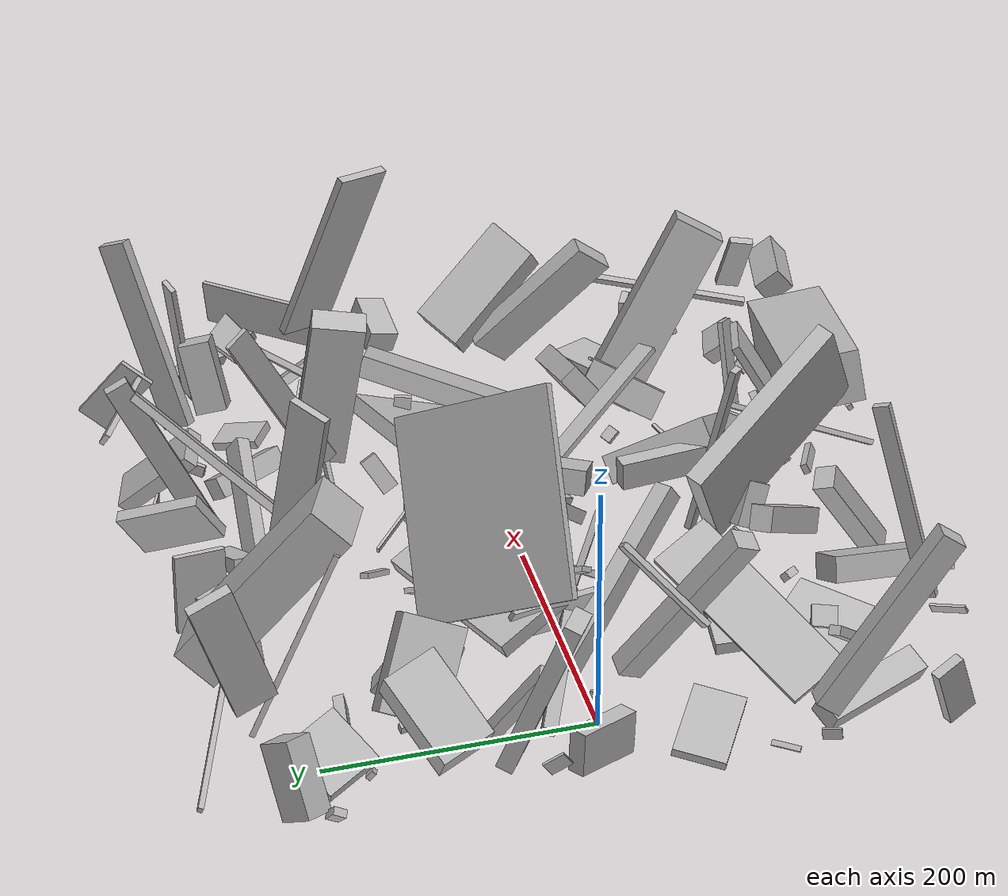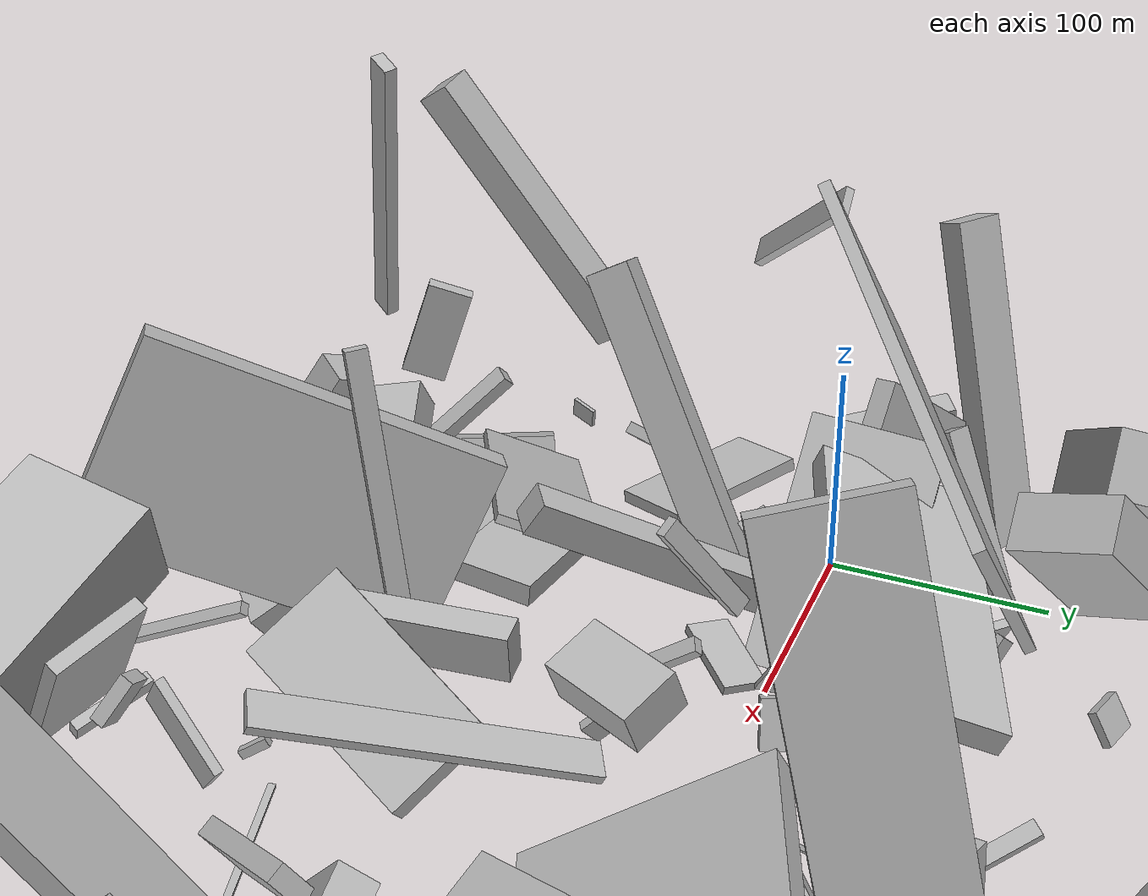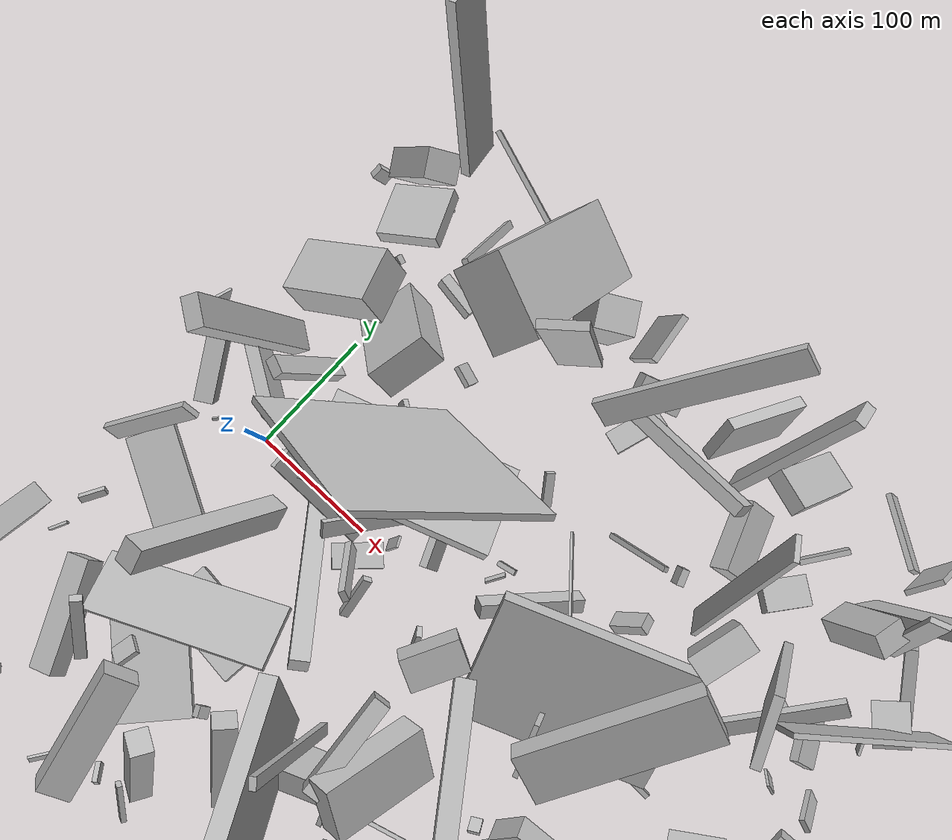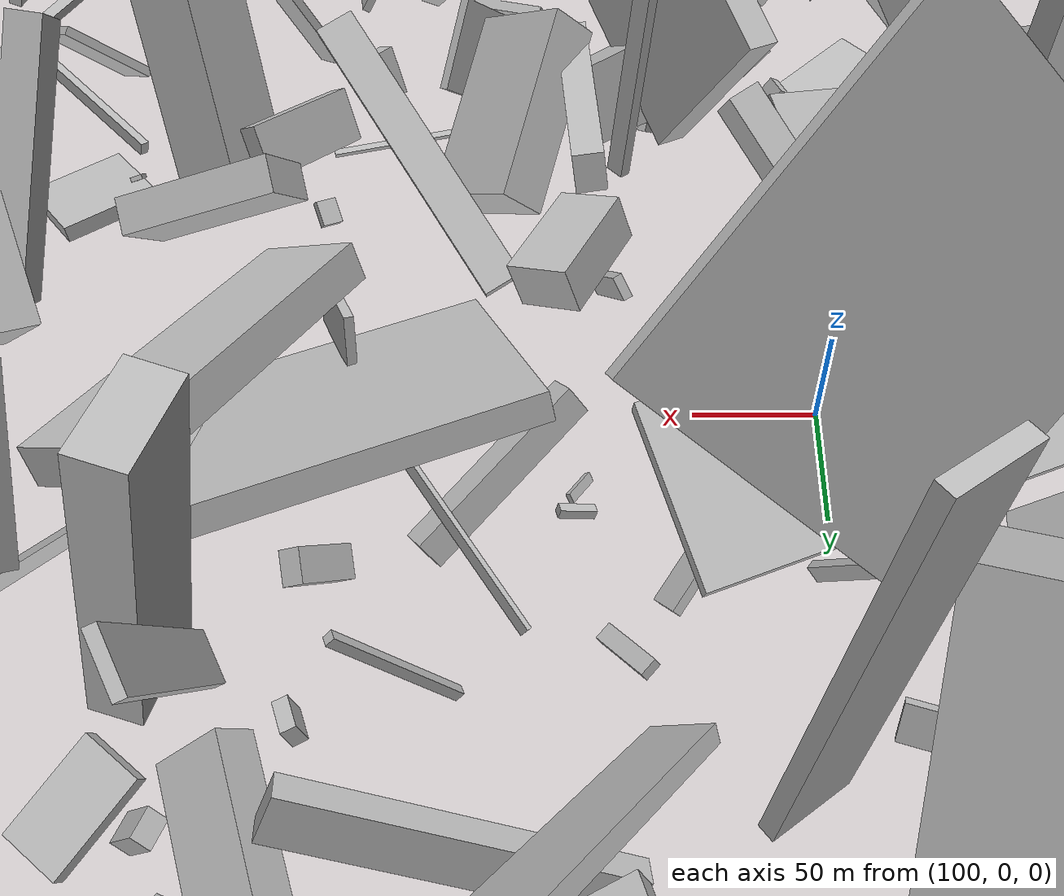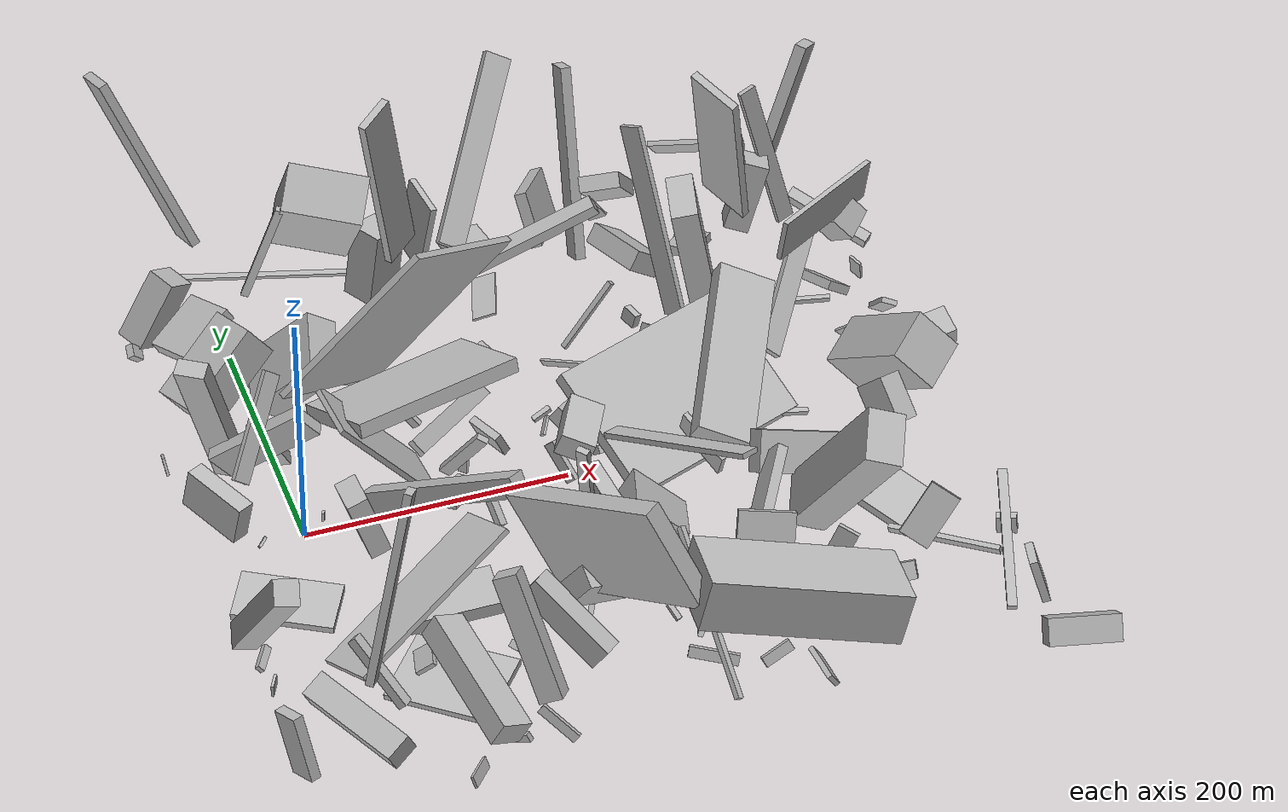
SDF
<sdf version="1.6">
 <world name="default">
  <scene>
   <sky><clouds><speed>12</speed></clouds></sky>
   <ambient>0.4 0.4 0.4 1</ambient>
   <background>0.7 0.7 0.7 1</background>
   <shadows>1</shadows>
  </scene>
  <gravity>0 0 -9.8066</gravity>
  <magnetic_field>6e-06 2.3e-05 -4.2e-05</magnetic_field>
  <physics default="0" name="default_physics" type="ode">
   <ode>
    <solver>
     <type>quick</type>
     <iters>10</iters>
     <sor>1.0</sor>
     <use_dynamic_moi_rescaling>0</use_dynamic_moi_rescaling>
    </solver>
    <constraints>
     <cfm>0</cfm>
     <erp>0.2</erp>
     <contact_max_correcting_vel>100</contact_max_correcting_vel>
     <contact_surface_layer>0.001</contact_surface_layer>
    </constraints>
   </ode>
   <max_step_size>0.004</max_step_size>
   <real_time_factor>1</real_time_factor>
   <real_time_update_rate>250</real_time_update_rate>
  </physics>
  <light name="sun" type="directional">
   <pose>0 0 10 0 0 0</pose>
   <diffuse>0.8 0.8 0.8 1</diffuse>
   <specular>0.2 0.2 0.2 1</specular>
   <attenuation>
    <range>1000</range>
    <constant>0.9</constant>
    <linear>0.01</linear>
    <quadratic>0.001</quadratic>
   </attenuation>
   <direction>-0.5 0.1 -0.9</direction>
  </light>
  <model name="building_1">
   <static>0</static>
   <pose>241.0916509240941 -126.79172080091843 47.20947998207029 0.743622857691419 0.8195258798122124 -2.8497544787731073</pose>
   <link name="link">
    <gravity>0</gravity>
    <pose>0 0 22.5 0 0 0</pose>
    <collision name="collision"><geometry><box><size>22 82 45</size></box></geometry></collision>
    <visual name="visual">
     <cast_shadows>0</cast_shadows>
     <geometry><box><size>22 82 45</size></box></geometry>
     <material>
      <script>
       <uri>model://HANNAS_wall/materials/scripts</uri>
       <uri>model://HANNAS_wall/materials/textures</uri>
       <name>vrc/HANNAS_wall</name>
      </script>
     </material>
    </visual>
   </link>
  </model>
  <model name="building_2">
   <static>0</static>
   <pose>93.68266452927514 87.20159840653238 23.143579104200526 -0.08364449320465732 -0.8246747885361194 2.5702398322903472</pose>
   <link name="link">
    <gravity>0</gravity>
    <pose>0 0 3.5 0 0 0</pose>
    <collision name="collision"><geometry><box><size>46 4 7</size></box></geometry></collision>
    <visual name="visual">
     <cast_shadows>0</cast_shadows>
     <geometry><box><size>46 4 7</size></box></geometry>
     <material>
      <script>
       <uri>model://HANNAS_wall/materials/scripts</uri>
       <uri>model://HANNAS_wall/materials/textures</uri>
       <name>vrc/HANNAS_wall</name>
      </script>
     </material>
    </visual>
   </link>
  </model>
  <model name="building_3">
   <static>0</static>
   <pose>420.94607814986523 260.1127815754333 39.8420100999596 1.533527591717731 -0.6435940136169481 1.1607174363100758</pose>
   <link name="link">
    <gravity>0</gravity>
    <pose>0 0 2.0 0 0 0</pose>
    <collision name="collision"><geometry><box><size>28 61 4</size></box></geometry></collision>
    <visual name="visual">
     <cast_shadows>0</cast_shadows>
     <geometry><box><size>28 61 4</size></box></geometry>
     <material>
      <script>
       <uri>model://HANNAS_wall/materials/scripts</uri>
       <uri>model://HANNAS_wall/materials/textures</uri>
       <name>vrc/HANNAS_wall</name>
      </script>
     </material>
    </visual>
   </link>
  </model>
  <model name="building_4">
   <static>0</static>
   <pose>358.4666775041412 -253.40052799745908 62.26033274355591 1.2945197006456552 -0.1387699524928964 -1.6644033676453922</pose>
   <link name="link">
    <gravity>0</gravity>
    <pose>0 0 75.0 0 0 0</pose>
    <collision name="collision"><geometry><box><size>57 40 150</size></box></geometry></collision>
    <visual name="visual">
     <cast_shadows>0</cast_shadows>
     <geometry><box><size>57 40 150</size></box></geometry>
     <material>
      <script>
       <uri>model://HANNAS_wall/materials/scripts</uri>
       <uri>model://HANNAS_wall/materials/textures</uri>
       <name>vrc/HANNAS_wall</name>
      </script>
     </material>
    </visual>
   </link>
  </model>
  <model name="building_5">
   <static>0</static>
   <pose>46.39440185954816 -124.30378209727014 41.890652709012365 2.8159292976962544 0.37116564591501183 1.9308832724276412</pose>
   <link name="link">
    <gravity>0</gravity>
    <pose>0 0 2.0 0 0 0</pose>
    <collision name="collision"><geometry><box><size>48 150 4</size></box></geometry></collision>
    <visual name="visual">
     <cast_shadows>0</cast_shadows>
     <geometry><box><size>48 150 4</size></box></geometry>
     <material>
      <script>
       <uri>model://HANNAS_wall/materials/scripts</uri>
       <uri>model://HANNAS_wall/materials/textures</uri>
       <name>vrc/HANNAS_wall</name>
      </script>
     </material>
    </visual>
   </link>
  </model>
  <model name="building_6">
   <static>0</static>
   <pose>425.18389464368346 209.73645368273364 79.07927625135693 -0.7447193316424433 -1.3110439471025137 2.6268984074315966</pose>
   <link name="link">
    <gravity>0</gravity>
    <pose>0 0 2.0 0 0 0</pose>
    <collision name="collision"><geometry><box><size>124 14 4</size></box></geometry></collision>
    <visual name="visual">
     <cast_shadows>0</cast_shadows>
     <geometry><box><size>124 14 4</size></box></geometry>
     <material>
      <script>
       <uri>model://HANNAS_wall/materials/scripts</uri>
       <uri>model://HANNAS_wall/materials/textures</uri>
       <name>vrc/HANNAS_wall</name>
      </script>
     </material>
    </visual>
   </link>
  </model>
  <model name="building_7">
   <static>0</static>
   <pose>-20.88808407244128 -196.43720719920555 13.020495404349326 3.1354536858215885 -0.43932423467475895 0.45075643000725485</pose>
   <link name="link">
    <gravity>0</gravity>
    <pose>0 0 8.5 0 0 0</pose>
    <collision name="collision"><geometry><box><size>21 89 17</size></box></geometry></collision>
    <visual name="visual">
     <cast_shadows>0</cast_shadows>
     <geometry><box><size>21 89 17</size></box></geometry>
     <material>
      <script>
       <uri>model://HANNAS_wall/materials/scripts</uri>
       <uri>model://HANNAS_wall/materials/textures</uri>
       <name>vrc/HANNAS_wall</name>
      </script>
     </material>
    </visual>
   </link>
  </model>
  <model name="building_8">
   <static>0</static>
   <pose>-33.63528266691769 -71.66666681277462 12.464947994321324 -3.1287146317264773 -0.14972030072965373 1.068777617033211</pose>
   <link name="link">
    <gravity>0</gravity>
    <pose>0 0 3.0 0 0 0</pose>
    <collision name="collision"><geometry><box><size>39 75 6</size></box></geometry></collision>
    <visual name="visual">
     <cast_shadows>0</cast_shadows>
     <geometry><box><size>39 75 6</size></box></geometry>
     <material>
      <script>
       <uri>model://HANNAS_wall/materials/scripts</uri>
       <uri>model://HANNAS_wall/materials/textures</uri>
       <name>vrc/HANNAS_wall</name>
      </script>
     </material>
    </visual>
   </link>
  </model>
  <model name="building_9">
   <static>0</static>
   <pose>445.43260659078487 115.34296753509653 21.501391600132397 -0.3782642870587516 -0.850306131800718 0.7064850342172253</pose>
   <link name="link">
    <gravity>0</gravity>
    <pose>0 0 11.0 0 0 0</pose>
    <collision name="collision"><geometry><box><size>7 40 22</size></box></geometry></collision>
    <visual name="visual">
     <cast_shadows>0</cast_shadows>
     <geometry><box><size>7 40 22</size></box></geometry>
     <material>
      <script>
       <uri>model://HANNAS_wall/materials/scripts</uri>
       <uri>model://HANNAS_wall/materials/textures</uri>
       <name>vrc/HANNAS_wall</name>
      </script>
     </material>
    </visual>
   </link>
  </model>
  <model name="building_10">
   <static>0</static>
   <pose>331.610137652745 93.44440369719452 77.77424442970286 0.8828996320521553 -1.3547485997910766 -2.6844283307773633</pose>
   <link name="link">
    <gravity>0</gravity>
    <pose>0 0 20.0 0 0 0</pose>
    <collision name="collision"><geometry><box><size>138 20 40</size></box></geometry></collision>
    <visual name="visual">
     <cast_shadows>0</cast_shadows>
     <geometry><box><size>138 20 40</size></box></geometry>
     <material>
      <script>
       <uri>model://HANNAS_wall/materials/scripts</uri>
       <uri>model://HANNAS_wall/materials/textures</uri>
       <name>vrc/HANNAS_wall</name>
      </script>
     </material>
    </visual>
   </link>
  </model>
  <model name="building_11">
   <static>0</static>
   <pose>401.8039499982133 -173.39935292125682 31.49054169809454 -0.6019209860752779 0.462571180728749 -0.6685917153624122</pose>
   <link name="link">
    <gravity>0</gravity>
    <pose>0 0 21.5 0 0 0</pose>
    <collision name="collision"><geometry><box><size>24 4 43</size></box></geometry></collision>
    <visual name="visual">
     <cast_shadows>0</cast_shadows>
     <geometry><box><size>24 4 43</size></box></geometry>
     <material>
      <script>
       <uri>model://HANNAS_wall/materials/scripts</uri>
       <uri>model://HANNAS_wall/materials/textures</uri>
       <name>vrc/HANNAS_wall</name>
      </script>
     </material>
    </visual>
   </link>
  </model>
  <model name="building_12">
   <static>0</static>
   <pose>165.7694307742955 78.79263799654018 60.210648897042454 1.3180628031530128 1.1829132116903107 -1.4675095553041468</pose>
   <link name="link">
    <gravity>0</gravity>
    <pose>0 0 70.5 0 0 0</pose>
    <collision name="collision"><geometry><box><size>11 69 141</size></box></geometry></collision>
    <visual name="visual">
     <cast_shadows>0</cast_shadows>
     <geometry><box><size>11 69 141</size></box></geometry>
     <material>
      <script>
       <uri>model://HANNAS_wall/materials/scripts</uri>
       <uri>model://HANNAS_wall/materials/textures</uri>
       <name>vrc/HANNAS_wall</name>
      </script>
     </material>
    </visual>
   </link>
  </model>
  <model name="building_13">
   <static>0</static>
   <pose>-66.70951833344935 -116.61947152901874 9.21380651445296 2.3794854619025343 -0.09533255691385169 1.0499133881418117</pose>
   <link name="link">
    <gravity>0</gravity>
    <pose>0 0 3.0 0 0 0</pose>
    <collision name="collision"><geometry><box><size>21 4 6</size></box></geometry></collision>
    <visual name="visual">
     <cast_shadows>0</cast_shadows>
     <geometry><box><size>21 4 6</size></box></geometry>
     <material>
      <script>
       <uri>model://HANNAS_wall/materials/scripts</uri>
       <uri>model://HANNAS_wall/materials/textures</uri>
       <name>vrc/HANNAS_wall</name>
      </script>
     </material>
    </visual>
   </link>
  </model>
  <model name="building_14">
   <static>0</static>
   <pose>-20.372167882930636 123.33881018285552 49.520448993707554 0.5832452196303323 -0.24869577664676826 -1.240707007917855</pose>
   <link name="link">
    <gravity>0</gravity>
    <pose>0 0 15.0 0 0 0</pose>
    <collision name="collision"><geometry><box><size>42 72 30</size></box></geometry></collision>
    <visual name="visual">
     <cast_shadows>0</cast_shadows>
     <geometry><box><size>42 72 30</size></box></geometry>
     <material>
      <script>
       <uri>model://HANNAS_wall/materials/scripts</uri>
       <uri>model://HANNAS_wall/materials/textures</uri>
       <name>vrc/HANNAS_wall</name>
      </script>
     </material>
    </visual>
   </link>
  </model>
  <model name="building_15">
   <static>0</static>
   <pose>312.7719347964239 160.5705018023219 83.46617315777029 0.2651243395751293 -1.1004184875255292 1.7688924628607536</pose>
   <link name="link">
    <gravity>0</gravity>
    <pose>0 0 10.0 0 0 0</pose>
    <collision name="collision"><geometry><box><size>150 4 20</size></box></geometry></collision>
    <visual name="visual">
     <cast_shadows>0</cast_shadows>
     <geometry><box><size>150 4 20</size></box></geometry>
     <material>
      <script>
       <uri>model://HANNAS_wall/materials/scripts</uri>
       <uri>model://HANNAS_wall/materials/textures</uri>
       <name>vrc/HANNAS_wall</name>
      </script>
     </material>
    </visual>
   </link>
  </model>
  <model name="building_16">
   <static>0</static>
   <pose>424.6844603839976 117.50135674631075 10.533130628331943 3.0248042556646952 -0.09545040568449047 1.2489901597829198</pose>
   <link name="link">
    <gravity>0</gravity>
    <pose>0 0 2.0 0 0 0</pose>
    <collision name="collision"><geometry><box><size>4 40 4</size></box></geometry></collision>
    <visual name="visual">
     <cast_shadows>0</cast_shadows>
     <geometry><box><size>4 40 4</size></box></geometry>
     <material>
      <script>
       <uri>model://HANNAS_wall/materials/scripts</uri>
       <uri>model://HANNAS_wall/materials/textures</uri>
       <name>vrc/HANNAS_wall</name>
      </script>
     </material>
    </visual>
   </link>
  </model>
  <model name="building_17">
   <static>0</static>
   <pose>232.2137951948754 -227.86231759600875 21.878663982750652 -0.32473154866761295 1.0768451253514768 -2.2833988587806293</pose>
   <link name="link">
    <gravity>0</gravity>
    <pose>0 0 2.5 0 0 0</pose>
    <collision name="collision"><geometry><box><size>8 36 5</size></box></geometry></collision>
    <visual name="visual">
     <cast_shadows>0</cast_shadows>
     <geometry><box><size>8 36 5</size></box></geometry>
     <material>
      <script>
       <uri>model://HANNAS_wall/materials/scripts</uri>
       <uri>model://HANNAS_wall/materials/textures</uri>
       <name>vrc/HANNAS_wall</name>
      </script>
     </material>
    </visual>
   </link>
  </model>
  <model name="building_18">
   <static>0</static>
   <pose>166.54839110304812 -152.57960636875353 14.710386828490366 0.1613941632235688 -0.7294529193206175 1.019425712184774</pose>
   <link name="link">
    <gravity>0</gravity>
    <pose>0 0 2.0 0 0 0</pose>
    <collision name="collision"><geometry><box><size>9 4 4</size></box></geometry></collision>
    <visual name="visual">
     <cast_shadows>0</cast_shadows>
     <geometry><box><size>9 4 4</size></box></geometry>
     <material>
      <script>
       <uri>model://HANNAS_wall/materials/scripts</uri>
       <uri>model://HANNAS_wall/materials/textures</uri>
       <name>vrc/HANNAS_wall</name>
      </script>
     </material>
    </visual>
   </link>
  </model>
  <model name="building_19">
   <static>0</static>
   <pose>53.37094602882471 -228.86787353481577 47.1289597258935 -0.45692346735368955 0.21145087876503119 -1.3728973677016616</pose>
   <link name="link">
    <gravity>0</gravity>
    <pose>0 0 9.5 0 0 0</pose>
    <collision name="collision"><geometry><box><size>101 26 19</size></box></geometry></collision>
    <visual name="visual">
     <cast_shadows>0</cast_shadows>
     <geometry><box><size>101 26 19</size></box></geometry>
     <material>
      <script>
       <uri>model://HANNAS_wall/materials/scripts</uri>
       <uri>model://HANNAS_wall/materials/textures</uri>
       <name>vrc/HANNAS_wall</name>
      </script>
     </material>
    </visual>
   </link>
  </model>
  <model name="building_20">
   <static>0</static>
   <pose>172.75411120918056 -133.00806294383324 93.17697028687269 2.877991009944373 -1.365799307123116 -2.153895048102749</pose>
   <link name="link">
    <gravity>0</gravity>
    <pose>0 0 2.5 0 0 0</pose>
    <collision name="collision"><geometry><box><size>150 9 5</size></box></geometry></collision>
    <visual name="visual">
     <cast_shadows>0</cast_shadows>
     <geometry><box><size>150 9 5</size></box></geometry>
     <material>
      <script>
       <uri>model://HANNAS_wall/materials/scripts</uri>
       <uri>model://HANNAS_wall/materials/textures</uri>
       <name>vrc/HANNAS_wall</name>
      </script>
     </material>
    </visual>
   </link>
  </model>
  <model name="building_21">
   <static>0</static>
   <pose>69.91808612485723 -120.77039924723111 19.368061854004893 0.052684245216128196 0.09947499963649521 3.05177688670682</pose>
   <link name="link">
    <gravity>0</gravity>
    <pose>0 0 5.0 0 0 0</pose>
    <collision name="collision"><geometry><box><size>74 41 10</size></box></geometry></collision>
    <visual name="visual">
     <cast_shadows>0</cast_shadows>
     <geometry><box><size>74 41 10</size></box></geometry>
     <material>
      <script>
       <uri>model://HANNAS_wall/materials/scripts</uri>
       <uri>model://HANNAS_wall/materials/textures</uri>
       <name>vrc/HANNAS_wall</name>
      </script>
     </material>
    </visual>
   </link>
  </model>
  <model name="building_22">
   <static>0</static>
   <pose>137.21996340635576 100.89135735448768 96.95096128494049 0.9494818620397083 0.4326575226694881 -1.1258939234461234</pose>
   <link name="link">
    <gravity>0</gravity>
    <pose>0 0 75.0 0 0 0</pose>
    <collision name="collision"><geometry><box><size>5 150 150</size></box></geometry></collision>
    <visual name="visual">
     <cast_shadows>0</cast_shadows>
     <geometry><box><size>5 150 150</size></box></geometry>
     <material>
      <script>
       <uri>model://HANNAS_wall/materials/scripts</uri>
       <uri>model://HANNAS_wall/materials/textures</uri>
       <name>vrc/HANNAS_wall</name>
      </script>
     </material>
    </visual>
   </link>
  </model>
  <model name="building_23">
   <static>0</static>
   <pose>222.28202996532096 -3.8956743131773095 34.753353518337704 1.5868055997190684 -0.5030032479727464 1.937392350581111</pose>
   <link name="link">
    <gravity>0</gravity>
    <pose>0 0 75.0 0 0 0</pose>
    <collision name="collision"><geometry><box><size>106 12 150</size></box></geometry></collision>
    <visual name="visual">
     <cast_shadows>0</cast_shadows>
     <geometry><box><size>106 12 150</size></box></geometry>
     <material>
      <script>
       <uri>model://HANNAS_wall/materials/scripts</uri>
       <uri>model://HANNAS_wall/materials/textures</uri>
       <name>vrc/HANNAS_wall</name>
      </script>
     </material>
    </visual>
   </link>
  </model>
  <model name="building_24">
   <static>0</static>
   <pose>199.9052272344958 227.26171909071246 126.9411487804041 0.6526115121560769 -0.6063951936353014 0.9646820355856539</pose>
   <link name="link">
    <gravity>0</gravity>
    <pose>0 0 3.0 0 0 0</pose>
    <collision name="collision"><geometry><box><size>150 21 6</size></box></geometry></collision>
    <visual name="visual">
     <cast_shadows>0</cast_shadows>
     <geometry><box><size>150 21 6</size></box></geometry>
     <material>
      <script>
       <uri>model://HANNAS_wall/materials/scripts</uri>
       <uri>model://HANNAS_wall/materials/textures</uri>
       <name>vrc/HANNAS_wall</name>
      </script>
     </material>
    </visual>
   </link>
  </model>
  <model name="building_25">
   <static>0</static>
   <pose>254.02795782314413 -177.03393380565223 45.751858097996426 2.8392088810995095 -0.7404619568072064 -1.9102910947475058</pose>
   <link name="link">
    <gravity>0</gravity>
    <pose>0 0 22.5 0 0 0</pose>
    <collision name="collision"><geometry><box><size>42 4 45</size></box></geometry></collision>
    <visual name="visual">
     <cast_shadows>0</cast_shadows>
     <geometry><box><size>42 4 45</size></box></geometry>
     <material>
      <script>
       <uri>model://HANNAS_wall/materials/scripts</uri>
       <uri>model://HANNAS_wall/materials/textures</uri>
       <name>vrc/HANNAS_wall</name>
      </script>
     </material>
    </visual>
   </link>
  </model>
  <model name="building_26">
   <static>0</static>
   <pose>105.44713070205567 -210.74550809810407 68.68407914534313 -0.8655475477365348 -1.0071443820645478 1.924239164820859</pose>
   <link name="link">
    <gravity>0</gravity>
    <pose>0 0 8.0 0 0 0</pose>
    <collision name="collision"><geometry><box><size>96 18 16</size></box></geometry></collision>
    <visual name="visual">
     <cast_shadows>0</cast_shadows>
     <geometry><box><size>96 18 16</size></box></geometry>
     <material>
      <script>
       <uri>model://HANNAS_wall/materials/scripts</uri>
       <uri>model://HANNAS_wall/materials/textures</uri>
       <name>vrc/HANNAS_wall</name>
      </script>
     </material>
    </visual>
   </link>
  </model>
  <model name="building_27">
   <static>0</static>
   <pose>85.23500480755337 135.88356790974035 9.931502332318038 1.540888660692558 0.5594219313936739 -1.8960808070881332</pose>
   <link name="link">
    <gravity>0</gravity>
    <pose>0 0 8.5 0 0 0</pose>
    <collision name="collision"><geometry><box><size>4 16 17</size></box></geometry></collision>
    <visual name="visual">
     <cast_shadows>0</cast_shadows>
     <geometry><box><size>4 16 17</size></box></geometry>
     <material>
      <script>
       <uri>model://HANNAS_wall/materials/scripts</uri>
       <uri>model://HANNAS_wall/materials/textures</uri>
       <name>vrc/HANNAS_wall</name>
      </script>
     </material>
    </visual>
   </link>
  </model>
  <model name="building_28">
   <static>0</static>
   <pose>301.53153260046776 181.86867619258538 29.735204999669595 0.18532840897806316 -0.662983318759284 -2.916855498178971</pose>
   <link name="link">
    <gravity>0</gravity>
    <pose>0 0 8.0 0 0 0</pose>
    <collision name="collision"><geometry><box><size>28 54 16</size></box></geometry></collision>
    <visual name="visual">
     <cast_shadows>0</cast_shadows>
     <geometry><box><size>28 54 16</size></box></geometry>
     <material>
      <script>
       <uri>model://HANNAS_wall/materials/scripts</uri>
       <uri>model://HANNAS_wall/materials/textures</uri>
       <name>vrc/HANNAS_wall</name>
      </script>
     </material>
    </visual>
   </link>
  </model>
  <model name="building_29">
   <static>0</static>
   <pose>338.2036114047082 181.82612592009673 24.830610489536795 0.7201947805005466 0.07658988869370915 -1.8967467343626847</pose>
   <link name="link">
    <gravity>0</gravity>
    <pose>0 0 7.5 0 0 0</pose>
    <collision name="collision"><geometry><box><size>11 8 15</size></box></geometry></collision>
    <visual name="visual">
     <cast_shadows>0</cast_shadows>
     <geometry><box><size>11 8 15</size></box></geometry>
     <material>
      <script>
       <uri>model://HANNAS_wall/materials/scripts</uri>
       <uri>model://HANNAS_wall/materials/textures</uri>
       <name>vrc/HANNAS_wall</name>
      </script>
     </material>
    </visual>
   </link>
  </model>
  <model name="building_30">
   <static>0</static>
   <pose>352.5540884524679 -161.41338525035385 78.66194120069774 -0.6372867172122165 -0.9880449328464691 -1.258235981223565</pose>
   <link name="link">
    <gravity>0</gravity>
    <pose>0 0 19.5 0 0 0</pose>
    <collision name="collision"><geometry><box><size>150 28 39</size></box></geometry></collision>
    <visual name="visual">
     <cast_shadows>0</cast_shadows>
     <geometry><box><size>150 28 39</size></box></geometry>
     <material>
      <script>
       <uri>model://HANNAS_wall/materials/scripts</uri>
       <uri>model://HANNAS_wall/materials/textures</uri>
       <name>vrc/HANNAS_wall</name>
      </script>
     </material>
    </visual>
   </link>
  </model>
  <model name="building_31">
   <static>0</static>
   <pose>334.87711655066107 14.788009470166376 68.68643270497077 2.851370163803721 -0.42218061696903864 2.8121413530324255</pose>
   <link name="link">
    <gravity>0</gravity>
    <pose>0 0 8.0 0 0 0</pose>
    <collision name="collision"><geometry><box><size>44 143 16</size></box></geometry></collision>
    <visual name="visual">
     <cast_shadows>0</cast_shadows>
     <geometry><box><size>44 143 16</size></box></geometry>
     <material>
      <script>
       <uri>model://HANNAS_wall/materials/scripts</uri>
       <uri>model://HANNAS_wall/materials/textures</uri>
       <name>vrc/HANNAS_wall</name>
      </script>
     </material>
    </visual>
   </link>
  </model>
  <model name="building_32">
   <static>0</static>
   <pose>420.95966662323923 -84.94178865922247 60.43215980542375 0.8211074675303445 0.20617302497976223 -3.1090380642331135</pose>
   <link name="link">
    <gravity>0</gravity>
    <pose>0 0 17.5 0 0 0</pose>
    <collision name="collision"><geometry><box><size>14 115 35</size></box></geometry></collision>
    <visual name="visual">
     <cast_shadows>0</cast_shadows>
     <geometry><box><size>14 115 35</size></box></geometry>
     <material>
      <script>
       <uri>model://HANNAS_wall/materials/scripts</uri>
       <uri>model://HANNAS_wall/materials/textures</uri>
       <name>vrc/HANNAS_wall</name>
      </script>
     </material>
    </visual>
   </link>
  </model>
  <model name="building_33">
   <static>0</static>
   <pose>362.4078529921752 170.2658046078094 37.236047887932166 1.7301954655400793 -0.3510187998671166 -2.279040043163953</pose>
   <link name="link">
    <gravity>0</gravity>
    <pose>0 0 11.5 0 0 0</pose>
    <collision name="collision"><geometry><box><size>39 7 23</size></box></geometry></collision>
    <visual name="visual">
     <cast_shadows>0</cast_shadows>
     <geometry><box><size>39 7 23</size></box></geometry>
     <material>
      <script>
       <uri>model://HANNAS_wall/materials/scripts</uri>
       <uri>model://HANNAS_wall/materials/textures</uri>
       <name>vrc/HANNAS_wall</name>
      </script>
     </material>
    </visual>
   </link>
  </model>
  <model name="building_34">
   <static>0</static>
   <pose>64.80060387779892 22.05778503133563 53.35457951836982 2.2657699885645717 -0.10130988086096844 -1.5234121312381088</pose>
   <link name="link">
    <gravity>0</gravity>
    <pose>0 0 2.0 0 0 0</pose>
    <collision name="collision"><geometry><box><size>59 109 4</size></box></geometry></collision>
    <visual name="visual">
     <cast_shadows>0</cast_shadows>
     <geometry><box><size>59 109 4</size></box></geometry>
     <material>
      <script>
       <uri>model://HANNAS_wall/materials/scripts</uri>
       <uri>model://HANNAS_wall/materials/textures</uri>
       <name>vrc/HANNAS_wall</name>
      </script>
     </material>
    </visual>
   </link>
  </model>
  <model name="building_35">
   <static>0</static>
   <pose>-79.41641491042114 -189.5268638020601 109.38273346897822 -0.2862972918087752 -0.9384598453838635 -1.459430860747403</pose>
   <link name="link">
    <gravity>0</gravity>
    <pose>0 0 9.5 0 0 0</pose>
    <collision name="collision"><geometry><box><size>150 18 19</size></box></geometry></collision>
    <visual name="visual">
     <cast_shadows>0</cast_shadows>
     <geometry><box><size>150 18 19</size></box></geometry>
     <material>
      <script>
       <uri>model://HANNAS_wall/materials/scripts</uri>
       <uri>model://HANNAS_wall/materials/textures</uri>
       <name>vrc/HANNAS_wall</name>
      </script>
     </material>
    </visual>
   </link>
  </model>
  <model name="building_36">
   <static>0</static>
   <pose>344.7723852525848 -85.82009632368492 34.98490691655639 0.6406887320542455 -0.34330202802324283 -3.116895478110348</pose>
   <link name="link">
    <gravity>0</gravity>
    <pose>0 0 15.5 0 0 0</pose>
    <collision name="collision"><geometry><box><size>70 16 31</size></box></geometry></collision>
    <visual name="visual">
     <cast_shadows>0</cast_shadows>
     <geometry><box><size>70 16 31</size></box></geometry>
     <material>
      <script>
       <uri>model://HANNAS_wall/materials/scripts</uri>
       <uri>model://HANNAS_wall/materials/textures</uri>
       <name>vrc/HANNAS_wall</name>
      </script>
     </material>
    </visual>
   </link>
  </model>
  <model name="building_37">
   <static>0</static>
   <pose>147.36967346004366 -175.4206822387052 39.87576908829978 -1.318118748198189 -0.5494954403162317 2.2220988633181395</pose>
   <link name="link">
    <gravity>0</gravity>
    <pose>0 0 9.0 0 0 0</pose>
    <collision name="collision"><geometry><box><size>72 19 18</size></box></geometry></collision>
    <visual name="visual">
     <cast_shadows>0</cast_shadows>
     <geometry><box><size>72 19 18</size></box></geometry>
     <material>
      <script>
       <uri>model://HANNAS_wall/materials/scripts</uri>
       <uri>model://HANNAS_wall/materials/textures</uri>
       <name>vrc/HANNAS_wall</name>
      </script>
     </material>
    </visual>
   </link>
  </model>
  <model name="building_38">
   <static>0</static>
   <pose>28.284378417450245 209.25781398027644 90.7845851616711 1.8688683878801233 -0.3682445103963891 1.0635972946005239</pose>
   <link name="link">
    <gravity>0</gravity>
    <pose>0 0 3.0 0 0 0</pose>
    <collision name="collision"><geometry><box><size>4 150 6</size></box></geometry></collision>
    <visual name="visual">
     <cast_shadows>0</cast_shadows>
     <geometry><box><size>4 150 6</size></box></geometry>
     <material>
      <script>
       <uri>model://HANNAS_wall/materials/scripts</uri>
       <uri>model://HANNAS_wall/materials/textures</uri>
       <name>vrc/HANNAS_wall</name>
      </script>
     </material>
    </visual>
   </link>
  </model>
  <model name="building_39">
   <static>0</static>
   <pose>306.875966251606 -257.0847921308212 10.31073312570015 0.15388736754576282 -0.5339724337595798 0.07219591271736593</pose>
   <link name="link">
    <gravity>0</gravity>
    <pose>0 0 7.5 0 0 0</pose>
    <collision name="collision"><geometry><box><size>4 29 15</size></box></geometry></collision>
    <visual name="visual">
     <cast_shadows>0</cast_shadows>
     <geometry><box><size>4 29 15</size></box></geometry>
     <material>
      <script>
       <uri>model://HANNAS_wall/materials/scripts</uri>
       <uri>model://HANNAS_wall/materials/textures</uri>
       <name>vrc/HANNAS_wall</name>
      </script>
     </material>
    </visual>
   </link>
  </model>
  <model name="building_40">
   <static>0</static>
   <pose>102.72367714056759 -175.6460112231005 22.458659909224217 2.463916593694222 0.12068947253872109 2.0791542861998233</pose>
   <link name="link">
    <gravity>0</gravity>
    <pose>0 0 5.0 0 0 0</pose>
    <collision name="collision"><geometry><box><size>9 6 10</size></box></geometry></collision>
    <visual name="visual">
     <cast_shadows>0</cast_shadows>
     <geometry><box><size>9 6 10</size></box></geometry>
     <material>
      <script>
       <uri>model://HANNAS_wall/materials/scripts</uri>
       <uri>model://HANNAS_wall/materials/textures</uri>
       <name>vrc/HANNAS_wall</name>
      </script>
     </material>
    </visual>
   </link>
  </model>
  <model name="building_41">
   <static>0</static>
   <pose>278.8359966370547 -197.91882227467732 79.99541068362628 1.0383896606435579 0.10825217130933673 -0.26533853469157304</pose>
   <link name="link">
    <gravity>0</gravity>
    <pose>0 0 3.0 0 0 0</pose>
    <collision name="collision"><geometry><box><size>41 60 6</size></box></geometry></collision>
    <visual name="visual">
     <cast_shadows>0</cast_shadows>
     <geometry><box><size>41 60 6</size></box></geometry>
     <material>
      <script>
       <uri>model://HANNAS_wall/materials/scripts</uri>
       <uri>model://HANNAS_wall/materials/textures</uri>
       <name>vrc/HANNAS_wall</name>
      </script>
     </material>
    </visual>
   </link>
  </model>
  <model name="building_42">
   <static>0</static>
   <pose>-47.49686942183379 49.06012062323134 41.91287537348437 -0.27753428216767756 -0.8786318154192166 3.014544155904634</pose>
   <link name="link">
    <gravity>0</gravity>
    <pose>0 0 42.0 0 0 0</pose>
    <collision name="collision"><geometry><box><size>26 10 84</size></box></geometry></collision>
    <visual name="visual">
     <cast_shadows>0</cast_shadows>
     <geometry><box><size>26 10 84</size></box></geometry>
     <material>
      <script>
       <uri>model://HANNAS_wall/materials/scripts</uri>
       <uri>model://HANNAS_wall/materials/textures</uri>
       <name>vrc/HANNAS_wall</name>
      </script>
     </material>
    </visual>
   </link>
  </model>
  <model name="building_43">
   <static>0</static>
   <pose>69.83556680383288 203.09176957778536 101.23985169781314 -0.3007889731777327 -0.8596261379734641 -1.7079117507405144</pose>
   <link name="link">
    <gravity>0</gravity>
    <pose>0 0 18.0 0 0 0</pose>
    <collision name="collision"><geometry><box><size>150 60 36</size></box></geometry></collision>
    <visual name="visual">
     <cast_shadows>0</cast_shadows>
     <geometry><box><size>150 60 36</size></box></geometry>
     <material>
      <script>
       <uri>model://HANNAS_wall/materials/scripts</uri>
       <uri>model://HANNAS_wall/materials/textures</uri>
       <name>vrc/HANNAS_wall</name>
      </script>
     </material>
    </visual>
   </link>
  </model>
  <model name="building_44">
   <static>0</static>
   <pose>301.9351442187228 -46.75546142897778 20.392710485427443 1.1989342795985283 0.14700428645064403 -2.802006148436545</pose>
   <link name="link">
    <gravity>0</gravity>
    <pose>0 0 22.5 0 0 0</pose>
    <collision name="collision"><geometry><box><size>4 23 45</size></box></geometry></collision>
    <visual name="visual">
     <cast_shadows>0</cast_shadows>
     <geometry><box><size>4 23 45</size></box></geometry>
     <material>
      <script>
       <uri>model://HANNAS_wall/materials/scripts</uri>
       <uri>model://HANNAS_wall/materials/textures</uri>
       <name>vrc/HANNAS_wall</name>
      </script>
     </material>
    </visual>
   </link>
  </model>
  <model name="building_45">
   <static>0</static>
   <pose>311.39756330672935 243.1435573272389 41.89936518291971 0.27945418709858466 -0.7817726247774739 -2.099672538147056</pose>
   <link name="link">
    <gravity>0</gravity>
    <pose>0 0 6.0 0 0 0</pose>
    <collision name="collision"><geometry><box><size>76 31 12</size></box></geometry></collision>
    <visual name="visual">
     <cast_shadows>0</cast_shadows>
     <geometry><box><size>76 31 12</size></box></geometry>
     <material>
      <script>
       <uri>model://HANNAS_wall/materials/scripts</uri>
       <uri>model://HANNAS_wall/materials/textures</uri>
       <name>vrc/HANNAS_wall</name>
      </script>
     </material>
    </visual>
   </link>
  </model>
  <model name="building_46">
   <static>0</static>
   <pose>472.34040938059667 39.89302498321749 16.53469781019052 1.3953370975488293 -0.25349371672211796 1.665510111453216</pose>
   <link name="link">
    <gravity>0</gravity>
    <pose>0 0 21.0 0 0 0</pose>
    <collision name="collision"><geometry><box><size>23 17 42</size></box></geometry></collision>
    <visual name="visual">
     <cast_shadows>0</cast_shadows>
     <geometry><box><size>23 17 42</size></box></geometry>
     <material>
      <script>
       <uri>model://HANNAS_wall/materials/scripts</uri>
       <uri>model://HANNAS_wall/materials/textures</uri>
       <name>vrc/HANNAS_wall</name>
      </script>
     </material>
    </visual>
   </link>
  </model>
  <model name="building_47">
   <static>0</static>
   <pose>109.0889774042771 -257.7520618457164 23.023382390922706 -1.1105572702726605 -0.5054832712852971 2.307715222663367</pose>
   <link name="link">
    <gravity>0</gravity>
    <pose>0 0 2.0 0 0 0</pose>
    <collision name="collision"><geometry><box><size>33 7 4</size></box></geometry></collision>
    <visual name="visual">
     <cast_shadows>0</cast_shadows>
     <geometry><box><size>33 7 4</size></box></geometry>
     <material>
      <script>
       <uri>model://HANNAS_wall/materials/scripts</uri>
       <uri>model://HANNAS_wall/materials/textures</uri>
       <name>vrc/HANNAS_wall</name>
      </script>
     </material>
    </visual>
   </link>
  </model>
  <model name="building_48">
   <static>0</static>
   <pose>-18.881085516521118 169.15855055549522 9.037258919037775 -2.297347851545211 -0.24849904969051714 2.822047316341963</pose>
   <link name="link">
    <gravity>0</gravity>
    <pose>0 0 2.0 0 0 0</pose>
    <collision name="collision"><geometry><box><size>7 7 4</size></box></geometry></collision>
    <visual name="visual">
     <cast_shadows>0</cast_shadows>
     <geometry><box><size>7 7 4</size></box></geometry>
     <material>
      <script>
       <uri>model://HANNAS_wall/materials/scripts</uri>
       <uri>model://HANNAS_wall/materials/textures</uri>
       <name>vrc/HANNAS_wall</name>
      </script>
     </material>
    </visual>
   </link>
  </model>
  <model name="building_49">
   <static>0</static>
   <pose>407.3927169293918 102.85648008044618 37.097169434354186 2.685153396075238 -0.704578156372444 2.856440209679278</pose>
   <link name="link">
    <gravity>0</gravity>
    <pose>0 0 2.5 0 0 0</pose>
    <collision name="collision"><geometry><box><size>17 109 5</size></box></geometry></collision>
    <visual name="visual">
     <cast_shadows>0</cast_shadows>
     <geometry><box><size>17 109 5</size></box></geometry>
     <material>
      <script>
       <uri>model://HANNAS_wall/materials/scripts</uri>
       <uri>model://HANNAS_wall/materials/textures</uri>
       <name>vrc/HANNAS_wall</name>
      </script>
     </material>
    </visual>
   </link>
  </model>
  <model name="building_50">
   <static>0</static>
   <pose>464.64126286155783 -244.9095397115728 44.515205050815545 1.2922818838705907 -0.17346900817525696 1.4109254514971754</pose>
   <link name="link">
    <gravity>0</gravity>
    <pose>0 0 3.0 0 0 0</pose>
    <collision name="collision"><geometry><box><size>18 51 6</size></box></geometry></collision>
    <visual name="visual">
     <cast_shadows>0</cast_shadows>
     <geometry><box><size>18 51 6</size></box></geometry>
     <material>
      <script>
       <uri>model://HANNAS_wall/materials/scripts</uri>
       <uri>model://HANNAS_wall/materials/textures</uri>
       <name>vrc/HANNAS_wall</name>
      </script>
     </material>
    </visual>
   </link>
  </model>
  <model name="building_51">
   <static>0</static>
   <pose>429.20433102627374 -167.71950130565415 21.08821913895362 1.8471695355706919 -0.13456763340078798 -0.7459247431739277</pose>
   <link name="link">
    <gravity>0</gravity>
    <pose>0 0 2.0 0 0 0</pose>
    <collision name="collision"><geometry><box><size>86 6 4</size></box></geometry></collision>
    <visual name="visual">
     <cast_shadows>0</cast_shadows>
     <geometry><box><size>86 6 4</size></box></geometry>
     <material>
      <script>
       <uri>model://HANNAS_wall/materials/scripts</uri>
       <uri>model://HANNAS_wall/materials/textures</uri>
       <name>vrc/HANNAS_wall</name>
      </script>
     </material>
    </visual>
   </link>
  </model>
  <model name="building_52">
   <static>0</static>
   <pose>-18.72388167998588 222.7443631146848 9.943317451530543 1.3968502560996974 0.17037749411433595 1.2557903740939866</pose>
   <link name="link">
    <gravity>0</gravity>
    <pose>0 0 2.0 0 0 0</pose>
    <collision name="collision"><geometry><box><size>4 4 4</size></box></geometry></collision>
    <visual name="visual">
     <cast_shadows>0</cast_shadows>
     <geometry><box><size>4 4 4</size></box></geometry>
     <material>
      <script>
       <uri>model://HANNAS_wall/materials/scripts</uri>
       <uri>model://HANNAS_wall/materials/textures</uri>
       <name>vrc/HANNAS_wall</name>
      </script>
     </material>
    </visual>
   </link>
  </model>
  <model name="building_53">
   <static>0</static>
   <pose>203.32543652585144 -145.4382600590696 30.97249290845363 0.9346104282706533 -0.9587643377372761 -0.7359608823115944</pose>
   <link name="link">
    <gravity>0</gravity>
    <pose>0 0 29.0 0 0 0</pose>
    <collision name="collision"><geometry><box><size>34 18 58</size></box></geometry></collision>
    <visual name="visual">
     <cast_shadows>0</cast_shadows>
     <geometry><box><size>34 18 58</size></box></geometry>
     <material>
      <script>
       <uri>model://HANNAS_wall/materials/scripts</uri>
       <uri>model://HANNAS_wall/materials/textures</uri>
       <name>vrc/HANNAS_wall</name>
      </script>
     </material>
    </visual>
   </link>
  </model>
  <model name="building_54">
   <static>0</static>
   <pose>450.9887812455356 -35.7184766322068 63.605488287098986 0.5012935734411316 -0.6474163289088832 -1.2074735683968052</pose>
   <link name="link">
    <gravity>0</gravity>
    <pose>0 0 20.0 0 0 0</pose>
    <collision name="collision"><geometry><box><size>90 39 40</size></box></geometry></collision>
    <visual name="visual">
     <cast_shadows>0</cast_shadows>
     <geometry><box><size>90 39 40</size></box></geometry>
     <material>
      <script>
       <uri>model://HANNAS_wall/materials/scripts</uri>
       <uri>model://HANNAS_wall/materials/textures</uri>
       <name>vrc/HANNAS_wall</name>
      </script>
     </material>
    </visual>
   </link>
  </model>
  <model name="building_55">
   <static>0</static>
   <pose>97.22893859181868 -27.22976667570987 25.451646081683496 2.4077476180737194 -1.3746284531680037 1.50992494136302</pose>
   <link name="link">
    <gravity>0</gravity>
    <pose>0 0 19.0 0 0 0</pose>
    <collision name="collision"><geometry><box><size>4 19 38</size></box></geometry></collision>
    <visual name="visual">
     <cast_shadows>0</cast_shadows>
     <geometry><box><size>4 19 38</size></box></geometry>
     <material>
      <script>
       <uri>model://HANNAS_wall/materials/scripts</uri>
       <uri>model://HANNAS_wall/materials/textures</uri>
       <name>vrc/HANNAS_wall</name>
      </script>
     </material>
    </visual>
   </link>
  </model>
  <model name="building_56">
   <static>0</static>
   <pose>-1.418409325611036 -185.5306454842825 36.705620705198925 0.7376782357435233 0.2413145972297355 0.8109978898056613</pose>
   <link name="link">
    <gravity>0</gravity>
    <pose>0 0 3.5 0 0 0</pose>
    <collision name="collision"><geometry><box><size>9 59 7</size></box></geometry></collision>
    <visual name="visual">
     <cast_shadows>0</cast_shadows>
     <geometry><box><size>9 59 7</size></box></geometry>
     <material>
      <script>
       <uri>model://HANNAS_wall/materials/scripts</uri>
       <uri>model://HANNAS_wall/materials/textures</uri>
       <name>vrc/HANNAS_wall</name>
      </script>
     </material>
    </visual>
   </link>
  </model>
  <model name="building_57">
   <static>0</static>
   <pose>297.3421806104428 131.80509754937646 10.710543558785393 1.4596949716810643 -0.23183894567077598 -2.7416501825292756</pose>
   <link name="link">
    <gravity>0</gravity>
    <pose>0 0 6.5 0 0 0</pose>
    <collision name="collision"><geometry><box><size>6 11 13</size></box></geometry></collision>
    <visual name="visual">
     <cast_shadows>0</cast_shadows>
     <geometry><box><size>6 11 13</size></box></geometry>
     <material>
      <script>
       <uri>model://HANNAS_wall/materials/scripts</uri>
       <uri>model://HANNAS_wall/materials/textures</uri>
       <name>vrc/HANNAS_wall</name>
      </script>
     </material>
    </visual>
   </link>
  </model>
  <model name="building_58">
   <static>0</static>
   <pose>390.155040526304 -209.44246681990393 39.19762140845673 1.826163952804419 -0.7236364658055908 -2.0004751579557314</pose>
   <link name="link">
    <gravity>0</gravity>
    <pose>0 0 13.0 0 0 0</pose>
    <collision name="collision"><geometry><box><size>24 13 26</size></box></geometry></collision>
    <visual name="visual">
     <cast_shadows>0</cast_shadows>
     <geometry><box><size>24 13 26</size></box></geometry>
     <material>
      <script>
       <uri>model://HANNAS_wall/materials/scripts</uri>
       <uri>model://HANNAS_wall/materials/textures</uri>
       <name>vrc/HANNAS_wall</name>
      </script>
     </material>
    </visual>
   </link>
  </model>
  <model name="building_59">
   <static>0</static>
   <pose>165.554528659066 -180.96758055557927 98.78134703752377 1.2275736127695838 -1.0695009115556346 2.4516035722868086</pose>
   <link name="link">
    <gravity>0</gravity>
    <pose>0 0 7.0 0 0 0</pose>
    <collision name="collision"><geometry><box><size>86 150 14</size></box></geometry></collision>
    <visual name="visual">
     <cast_shadows>0</cast_shadows>
     <geometry><box><size>86 150 14</size></box></geometry>
     <material>
      <script>
       <uri>model://HANNAS_wall/materials/scripts</uri>
       <uri>model://HANNAS_wall/materials/textures</uri>
       <name>vrc/HANNAS_wall</name>
      </script>
     </material>
    </visual>
   </link>
  </model>
  <model name="building_60">
   <static>0</static>
   <pose>471.3736044733044 85.56573062009826 15.087416893283951 0.6635283891658516 0.36113583488974227 -0.3124146970888122</pose>
   <link name="link">
    <gravity>0</gravity>
    <pose>0 0 15.0 0 0 0</pose>
    <collision name="collision"><geometry><box><size>12 4 30</size></box></geometry></collision>
    <visual name="visual">
     <cast_shadows>0</cast_shadows>
     <geometry><box><size>12 4 30</size></box></geometry>
     <material>
      <script>
       <uri>model://HANNAS_wall/materials/scripts</uri>
       <uri>model://HANNAS_wall/materials/textures</uri>
       <name>vrc/HANNAS_wall</name>
      </script>
     </material>
    </visual>
   </link>
  </model>
  <model name="building_61">
   <static>0</static>
   <pose>197.72634008904322 54.88276212324006 11.811310811559455 0.17302855116467286 -0.3605078757301616 0.20998635471627788</pose>
   <link name="link">
    <gravity>0</gravity>
    <pose>0 0 2.0 0 0 0</pose>
    <collision name="collision"><geometry><box><size>15 4 4</size></box></geometry></collision>
    <visual name="visual">
     <cast_shadows>0</cast_shadows>
     <geometry><box><size>15 4 4</size></box></geometry>
     <material>
      <script>
       <uri>model://HANNAS_wall/materials/scripts</uri>
       <uri>model://HANNAS_wall/materials/textures</uri>
       <name>vrc/HANNAS_wall</name>
      </script>
     </material>
    </visual>
   </link>
  </model>
  <model name="building_62">
   <static>0</static>
   <pose>274.96807584200036 -265.9943412545197 54.83317999680026 -1.977334174896607 0.5031958168412397 1.5465730959121566</pose>
   <link name="link">
    <gravity>0</gravity>
    <pose>0 0 11.5 0 0 0</pose>
    <collision name="collision"><geometry><box><size>4 8 23</size></box></geometry></collision>
    <visual name="visual">
     <cast_shadows>0</cast_shadows>
     <geometry><box><size>4 8 23</size></box></geometry>
     <material>
      <script>
       <uri>model://HANNAS_wall/materials/scripts</uri>
       <uri>model://HANNAS_wall/materials/textures</uri>
       <name>vrc/HANNAS_wall</name>
      </script>
     </material>
    </visual>
   </link>
  </model>
  <model name="building_63">
   <static>0</static>
   <pose>82.45734863095024 -258.82880054038515 14.68056365023812 0.10681894596541489 -0.46822764057442184 -0.8764895262995303</pose>
   <link name="link">
    <gravity>0</gravity>
    <pose>0 0 3.5 0 0 0</pose>
    <collision name="collision"><geometry><box><size>15 4 7</size></box></geometry></collision>
    <visual name="visual">
     <cast_shadows>0</cast_shadows>
     <geometry><box><size>15 4 7</size></box></geometry>
     <material>
      <script>
       <uri>model://HANNAS_wall/materials/scripts</uri>
       <uri>model://HANNAS_wall/materials/textures</uri>
       <name>vrc/HANNAS_wall</name>
      </script>
     </material>
    </visual>
   </link>
  </model>
  <model name="building_64">
   <static>0</static>
   <pose>224.69186396211842 -176.15402441559422 9.813193448002359 -1.0438552306481101 -0.14515546488405412 0.3041412732127667</pose>
   <link name="link">
    <gravity>0</gravity>
    <pose>0 0 6.5 0 0 0</pose>
    <collision name="collision"><geometry><box><size>4 4 13</size></box></geometry></collision>
    <visual name="visual">
     <cast_shadows>0</cast_shadows>
     <geometry><box><size>4 4 13</size></box></geometry>
     <material>
      <script>
       <uri>model://HANNAS_wall/materials/scripts</uri>
       <uri>model://HANNAS_wall/materials/textures</uri>
       <name>vrc/HANNAS_wall</name>
      </script>
     </material>
    </visual>
   </link>
  </model>
  <model name="building_65">
   <static>0</static>
   <pose>363.66978561794576 124.71787233094415 119.49635064414747 0.18732641418825172 -0.2750737908505673 0.41745687337188275</pose>
   <link name="link">
    <gravity>0</gravity>
    <pose>0 0 75.0 0 0 0</pose>
    <collision name="collision"><geometry><box><size>6 42 150</size></box></geometry></collision>
    <visual name="visual">
     <cast_shadows>0</cast_shadows>
     <geometry><box><size>6 42 150</size></box></geometry>
     <material>
      <script>
       <uri>model://HANNAS_wall/materials/scripts</uri>
       <uri>model://HANNAS_wall/materials/textures</uri>
       <name>vrc/HANNAS_wall</name>
      </script>
     </material>
    </visual>
   </link>
  </model>
  <model name="building_66">
   <static>0</static>
   <pose>130.99200724072716 223.94469082857685 35.920538909771686 1.566359889652618 -0.186672583721242 -2.596067929572076</pose>
   <link name="link">
    <gravity>0</gravity>
    <pose>0 0 13.0 0 0 0</pose>
    <collision name="collision"><geometry><box><size>31 59 26</size></box></geometry></collision>
    <visual name="visual">
     <cast_shadows>0</cast_shadows>
     <geometry><box><size>31 59 26</size></box></geometry>
     <material>
      <script>
       <uri>model://HANNAS_wall/materials/scripts</uri>
       <uri>model://HANNAS_wall/materials/textures</uri>
       <name>vrc/HANNAS_wall</name>
      </script>
     </material>
    </visual>
   </link>
  </model>
  <model name="building_67">
   <static>0</static>
   <pose>228.79883241764915 -222.56830623551357 58.71533889671281 2.186517972011142 -0.4679932095062374 1.5947183331059671</pose>
   <link name="link">
    <gravity>0</gravity>
    <pose>0 0 2.5 0 0 0</pose>
    <collision name="collision"><geometry><box><size>131 4 5</size></box></geometry></collision>
    <visual name="visual">
     <cast_shadows>0</cast_shadows>
     <geometry><box><size>131 4 5</size></box></geometry>
     <material>
      <script>
       <uri>model://HANNAS_wall/materials/scripts</uri>
       <uri>model://HANNAS_wall/materials/textures</uri>
       <name>vrc/HANNAS_wall</name>
      </script>
     </material>
    </visual>
   </link>
  </model>
  <model name="building_68">
   <static>0</static>
   <pose>132.36002529619157 192.21474037690226 79.83747048862682 -0.18618379834541562 -0.0009575086480945377 2.2409310775673466</pose>
   <link name="link">
    <gravity>0</gravity>
    <pose>0 0 75.0 0 0 0</pose>
    <collision name="collision"><geometry><box><size>6 31 150</size></box></geometry></collision>
    <visual name="visual">
     <cast_shadows>0</cast_shadows>
     <geometry><box><size>6 31 150</size></box></geometry>
     <material>
      <script>
       <uri>model://HANNAS_wall/materials/scripts</uri>
       <uri>model://HANNAS_wall/materials/textures</uri>
       <name>vrc/HANNAS_wall</name>
      </script>
     </material>
    </visual>
   </link>
  </model>
  <model name="building_69">
   <static>0</static>
   <pose>-47.369382195028074 59.040507682319664 83.64216622408469 1.921511300989764 -0.044116707575975245 -0.6120129374265885</pose>
   <link name="link">
    <gravity>0</gravity>
    <pose>0 0 6.5 0 0 0</pose>
    <collision name="collision"><geometry><box><size>23 150 13</size></box></geometry></collision>
    <visual name="visual">
     <cast_shadows>0</cast_shadows>
     <geometry><box><size>23 150 13</size></box></geometry>
     <material>
      <script>
       <uri>model://HANNAS_wall/materials/scripts</uri>
       <uri>model://HANNAS_wall/materials/textures</uri>
       <name>vrc/HANNAS_wall</name>
      </script>
     </material>
    </visual>
   </link>
  </model>
  <model name="building_70">
   <static>0</static>
   <pose>271.2309128674822 35.56702903592868 21.670190131776092 -1.431889999632938 -1.0156339978620255 1.9551152106547185</pose>
   <link name="link">
    <gravity>0</gravity>
    <pose>0 0 23.0 0 0 0</pose>
    <collision name="collision"><geometry><box><size>36 5 46</size></box></geometry></collision>
    <visual name="visual">
     <cast_shadows>0</cast_shadows>
     <geometry><box><size>36 5 46</size></box></geometry>
     <material>
      <script>
       <uri>model://HANNAS_wall/materials/scripts</uri>
       <uri>model://HANNAS_wall/materials/textures</uri>
       <name>vrc/HANNAS_wall</name>
      </script>
     </material>
    </visual>
   </link>
  </model>
  <model name="building_71">
   <static>0</static>
   <pose>330.1968036988453 -195.47994085437057 49.55689497154879 0.8915380532162503 -1.1391335186939078 0.006992334502852527</pose>
   <link name="link">
    <gravity>0</gravity>
    <pose>0 0 2.0 0 0 0</pose>
    <collision name="collision"><geometry><box><size>67 16 4</size></box></geometry></collision>
    <visual name="visual">
     <cast_shadows>0</cast_shadows>
     <geometry><box><size>67 16 4</size></box></geometry>
     <material>
      <script>
       <uri>model://HANNAS_wall/materials/scripts</uri>
       <uri>model://HANNAS_wall/materials/textures</uri>
       <name>vrc/HANNAS_wall</name>
      </script>
     </material>
    </visual>
   </link>
  </model>
  <model name="building_72">
   <static>0</static>
   <pose>282.1425946786053 256.8502933130008 74.10103031795215 0.20057346445343346 -1.137254127617539 1.4277439448821312</pose>
   <link name="link">
    <gravity>0</gravity>
    <pose>0 0 9.0 0 0 0</pose>
    <collision name="collision"><geometry><box><size>150 8 18</size></box></geometry></collision>
    <visual name="visual">
     <cast_shadows>0</cast_shadows>
     <geometry><box><size>150 8 18</size></box></geometry>
     <material>
      <script>
       <uri>model://HANNAS_wall/materials/scripts</uri>
       <uri>model://HANNAS_wall/materials/textures</uri>
       <name>vrc/HANNAS_wall</name>
      </script>
     </material>
    </visual>
   </link>
  </model>
  <model name="building_73">
   <static>0</static>
   <pose>87.26114988730603 -44.87804946665441 52.92675575512403 1.8418129628914812 -0.9970106331980924 1.9516563535127707</pose>
   <link name="link">
    <gravity>0</gravity>
    <pose>0 0 7.0 0 0 0</pose>
    <collision name="collision"><geometry><box><size>16 150 14</size></box></geometry></collision>
    <visual name="visual">
     <cast_shadows>0</cast_shadows>
     <geometry><box><size>16 150 14</size></box></geometry>
     <material>
      <script>
       <uri>model://HANNAS_wall/materials/scripts</uri>
       <uri>model://HANNAS_wall/materials/textures</uri>
       <name>vrc/HANNAS_wall</name>
      </script>
     </material>
    </visual>
   </link>
  </model>
  <model name="building_74">
   <static>0</static>
   <pose>188.69140222137554 -21.513581369356828 74.10458720812272 1.9101945912181952 -0.021617666772504103 1.0986745783191918</pose>
   <link name="link">
    <gravity>0</gravity>
    <pose>0 0 13.0 0 0 0</pose>
    <collision name="collision"><geometry><box><size>44 19 26</size></box></geometry></collision>
    <visual name="visual">
     <cast_shadows>0</cast_shadows>
     <geometry><box><size>44 19 26</size></box></geometry>
     <material>
      <script>
       <uri>model://HANNAS_wall/materials/scripts</uri>
       <uri>model://HANNAS_wall/materials/textures</uri>
       <name>vrc/HANNAS_wall</name>
      </script>
     </material>
    </visual>
   </link>
  </model>
  <model name="building_75">
   <static>0</static>
   <pose>178.11537149557103 117.10499241894999 21.31158583333841 0.33451323350801965 -0.4229480524214739 2.2319914269267005</pose>
   <link name="link">
    <gravity>0</gravity>
    <pose>0 0 2.0 0 0 0</pose>
    <collision name="collision"><geometry><box><size>27 7 4</size></box></geometry></collision>
    <visual name="visual">
     <cast_shadows>0</cast_shadows>
     <geometry><box><size>27 7 4</size></box></geometry>
     <material>
      <script>
       <uri>model://HANNAS_wall/materials/scripts</uri>
       <uri>model://HANNAS_wall/materials/textures</uri>
       <name>vrc/HANNAS_wall</name>
      </script>
     </material>
    </visual>
   </link>
  </model>
  <model name="building_76">
   <static>0</static>
   <pose>48.77249218777055 173.64844322874606 17.846482454891685 -1.3278862945001433 -1.348317301999412 1.1911420099555023</pose>
   <link name="link">
    <gravity>0</gravity>
    <pose>0 0 16.5 0 0 0</pose>
    <collision name="collision"><geometry><box><size>14 8 33</size></box></geometry></collision>
    <visual name="visual">
     <cast_shadows>0</cast_shadows>
     <geometry><box><size>14 8 33</size></box></geometry>
     <material>
      <script>
       <uri>model://HANNAS_wall/materials/scripts</uri>
       <uri>model://HANNAS_wall/materials/textures</uri>
       <name>vrc/HANNAS_wall</name>
      </script>
     </material>
    </visual>
   </link>
  </model>
  <model name="building_77">
   <static>0</static>
   <pose>253.69636535418607 -75.96792483671798 80.07160272130028 2.1571539125195676 -1.128843047515271 1.5498244398997585</pose>
   <link name="link">
    <gravity>0</gravity>
    <pose>0 0 8.0 0 0 0</pose>
    <collision name="collision"><geometry><box><size>4 130 16</size></box></geometry></collision>
    <visual name="visual">
     <cast_shadows>0</cast_shadows>
     <geometry><box><size>4 130 16</size></box></geometry>
     <material>
      <script>
       <uri>model://HANNAS_wall/materials/scripts</uri>
       <uri>model://HANNAS_wall/materials/textures</uri>
       <name>vrc/HANNAS_wall</name>
      </script>
     </material>
    </visual>
   </link>
  </model>
  <model name="building_78">
   <static>0</static>
   <pose>-62.27812065685185 15.898953788591594 21.125576892114417 0.15798727948010505 0.08745172113682435 0.54378119628999</pose>
   <link name="link">
    <gravity>0</gravity>
    <pose>0 0 16.0 0 0 0</pose>
    <collision name="collision"><geometry><box><size>14 51 32</size></box></geometry></collision>
    <visual name="visual">
     <cast_shadows>0</cast_shadows>
     <geometry><box><size>14 51 32</size></box></geometry>
     <material>
      <script>
       <uri>model://HANNAS_wall/materials/scripts</uri>
       <uri>model://HANNAS_wall/materials/textures</uri>
       <name>vrc/HANNAS_wall</name>
      </script>
     </material>
    </visual>
   </link>
  </model>
  <model name="building_79">
   <static>0</static>
   <pose>354.519049786812 4.133434508623265 11.349593220102234 -0.24568578435269803 -0.21486541041510893 3.123799538004072</pose>
   <link name="link">
    <gravity>0</gravity>
    <pose>0 0 2.0 0 0 0</pose>
    <collision name="collision"><geometry><box><size>65 4 4</size></box></geometry></collision>
    <visual name="visual">
     <cast_shadows>0</cast_shadows>
     <geometry><box><size>65 4 4</size></box></geometry>
     <material>
      <script>
       <uri>model://HANNAS_wall/materials/scripts</uri>
       <uri>model://HANNAS_wall/materials/textures</uri>
       <name>vrc/HANNAS_wall</name>
      </script>
     </material>
    </visual>
   </link>
  </model>
  <model name="building_80">
   <static>0</static>
   <pose>372.6041499995274 236.8039824002693 15.55378829828282 1.7659830259738687 0.13308532741557655 -0.5637382911734511</pose>
   <link name="link">
    <gravity>0</gravity>
    <pose>0 0 18.5 0 0 0</pose>
    <collision name="collision"><geometry><box><size>4 9 37</size></box></geometry></collision>
    <visual name="visual">
     <cast_shadows>0</cast_shadows>
     <geometry><box><size>4 9 37</size></box></geometry>
     <material>
      <script>
       <uri>model://HANNAS_wall/materials/scripts</uri>
       <uri>model://HANNAS_wall/materials/textures</uri>
       <name>vrc/HANNAS_wall</name>
      </script>
     </material>
    </visual>
   </link>
  </model>
  <model name="building_81">
   <static>0</static>
   <pose>397.29222194222456 -125.28781472322586 11.136324886141804 -1.410290852296442 -1.3288523689142844 -1.0780219402067424</pose>
   <link name="link">
    <gravity>0</gravity>
    <pose>0 0 21.5 0 0 0</pose>
    <collision name="collision"><geometry><box><size>7 43 43</size></box></geometry></collision>
    <visual name="visual">
     <cast_shadows>0</cast_shadows>
     <geometry><box><size>7 43 43</size></box></geometry>
     <material>
      <script>
       <uri>model://HANNAS_wall/materials/scripts</uri>
       <uri>model://HANNAS_wall/materials/textures</uri>
       <name>vrc/HANNAS_wall</name>
      </script>
     </material>
    </visual>
   </link>
  </model>
  <model name="building_82">
   <static>0</static>
   <pose>289.81705696104086 81.17236666611838 32.31120347654371 -2.331124700514804 -0.8193681155731473 0.7890446384309755</pose>
   <link name="link">
    <gravity>0</gravity>
    <pose>0 0 6.5 0 0 0</pose>
    <collision name="collision"><geometry><box><size>29 9 13</size></box></geometry></collision>
    <visual name="visual">
     <cast_shadows>0</cast_shadows>
     <geometry><box><size>29 9 13</size></box></geometry>
     <material>
      <script>
       <uri>model://HANNAS_wall/materials/scripts</uri>
       <uri>model://HANNAS_wall/materials/textures</uri>
       <name>vrc/HANNAS_wall</name>
      </script>
     </material>
    </visual>
   </link>
  </model>
  <model name="building_83">
   <static>0</static>
   <pose>395.3496469631721 189.48430048133156 34.098031935026576 0.2995405774979433 0.2557105146407037 1.2889898218066649</pose>
   <link name="link">
    <gravity>0</gravity>
    <pose>0 0 27.5 0 0 0</pose>
    <collision name="collision"><geometry><box><size>24 19 55</size></box></geometry></collision>
    <visual name="visual">
     <cast_shadows>0</cast_shadows>
     <geometry><box><size>24 19 55</size></box></geometry>
     <material>
      <script>
       <uri>model://HANNAS_wall/materials/scripts</uri>
       <uri>model://HANNAS_wall/materials/textures</uri>
       <name>vrc/HANNAS_wall</name>
      </script>
     </material>
    </visual>
   </link>
  </model>
  <model name="building_84">
   <static>0</static>
   <pose>124.23729328542301 40.18029710771225 45.108160155485905 2.6370424497698037 0.5878555015239595 -0.9474340844068958</pose>
   <link name="link">
    <gravity>0</gravity>
    <pose>0 0 2.0 0 0 0</pose>
    <collision name="collision"><geometry><box><size>13 150 4</size></box></geometry></collision>
    <visual name="visual">
     <cast_shadows>0</cast_shadows>
     <geometry><box><size>13 150 4</size></box></geometry>
     <material>
      <script>
       <uri>model://HANNAS_wall/materials/scripts</uri>
       <uri>model://HANNAS_wall/materials/textures</uri>
       <name>vrc/HANNAS_wall</name>
      </script>
     </material>
    </visual>
   </link>
  </model>
  <model name="building_85">
   <static>0</static>
   <pose>267.5312618815411 -204.6588740034895 50.622454474634736 0.5197828075598211 0.48116920991888074 -3.0189763221632675</pose>
   <link name="link">
    <gravity>0</gravity>
    <pose>0 0 10.5 0 0 0</pose>
    <collision name="collision"><geometry><box><size>12 6 21</size></box></geometry></collision>
    <visual name="visual">
     <cast_shadows>0</cast_shadows>
     <geometry><box><size>12 6 21</size></box></geometry>
     <material>
      <script>
       <uri>model://HANNAS_wall/materials/scripts</uri>
       <uri>model://HANNAS_wall/materials/textures</uri>
       <name>vrc/HANNAS_wall</name>
      </script>
     </material>
    </visual>
   </link>
  </model>
  <model name="building_86">
   <static>0</static>
   <pose>256.41580626919165 129.42878547802567 32.705676288039726 1.9176785914227064 -0.915418228511623 0.10843186354367944</pose>
   <link name="link">
    <gravity>0</gravity>
    <pose>0 0 2.0 0 0 0</pose>
    <collision name="collision"><geometry><box><size>63 4 4</size></box></geometry></collision>
    <visual name="visual">
     <cast_shadows>0</cast_shadows>
     <geometry><box><size>63 4 4</size></box></geometry>
     <material>
      <script>
       <uri>model://HANNAS_wall/materials/scripts</uri>
       <uri>model://HANNAS_wall/materials/textures</uri>
       <name>vrc/HANNAS_wall</name>
      </script>
     </material>
    </visual>
   </link>
  </model>
  <model name="building_87">
   <static>0</static>
   <pose>231.45055985048796 193.11529788467107 54.018008099867714 -1.1097898913725643 -0.4109266050710443 -0.07764631314791703</pose>
   <link name="link">
    <gravity>0</gravity>
    <pose>0 0 5.0 0 0 0</pose>
    <collision name="collision"><geometry><box><size>117 18 10</size></box></geometry></collision>
    <visual name="visual">
     <cast_shadows>0</cast_shadows>
     <geometry><box><size>117 18 10</size></box></geometry>
     <material>
      <script>
       <uri>model://HANNAS_wall/materials/scripts</uri>
       <uri>model://HANNAS_wall/materials/textures</uri>
       <name>vrc/HANNAS_wall</name>
      </script>
     </material>
    </visual>
   </link>
  </model>
  <model name="building_88">
   <static>0</static>
   <pose>445.64718784558613 138.7392388108753 76.29917300217241 1.8608739351352706 -1.3821792025103337 0.36155458472620566</pose>
   <link name="link">
    <gravity>0</gravity>
    <pose>0 0 2.0 0 0 0</pose>
    <collision name="collision"><geometry><box><size>32 119 4</size></box></geometry></collision>
    <visual name="visual">
     <cast_shadows>0</cast_shadows>
     <geometry><box><size>32 119 4</size></box></geometry>
     <material>
      <script>
       <uri>model://HANNAS_wall/materials/scripts</uri>
       <uri>model://HANNAS_wall/materials/textures</uri>
       <name>vrc/HANNAS_wall</name>
      </script>
     </material>
    </visual>
   </link>
  </model>
  <model name="building_89">
   <static>0</static>
   <pose>17.464132561246945 -70.21493888377765 70.9371083839635 1.2198749436579446 -0.4631684864807404 1.7948726797872083</pose>
   <link name="link">
    <gravity>0</gravity>
    <pose>0 0 8.0 0 0 0</pose>
    <collision name="collision"><geometry><box><size>20 150 16</size></box></geometry></collision>
    <visual name="visual">
     <cast_shadows>0</cast_shadows>
     <geometry><box><size>20 150 16</size></box></geometry>
     <material>
      <script>
       <uri>model://HANNAS_wall/materials/scripts</uri>
       <uri>model://HANNAS_wall/materials/textures</uri>
       <name>vrc/HANNAS_wall</name>
      </script>
     </material>
    </visual>
   </link>
  </model>
  <model name="building_90">
   <static>0</static>
   <pose>252.99321115076162 252.0266885678867 35.94722966042998 0.8636924829070604 -1.0375570867826212 1.8443578243213352</pose>
   <link name="link">
    <gravity>0</gravity>
    <pose>0 0 4.5 0 0 0</pose>
    <collision name="collision"><geometry><box><size>43 67 9</size></box></geometry></collision>
    <visual name="visual">
     <cast_shadows>0</cast_shadows>
     <geometry><box><size>43 67 9</size></box></geometry>
     <material>
      <script>
       <uri>model://HANNAS_wall/materials/scripts</uri>
       <uri>model://HANNAS_wall/materials/textures</uri>
       <name>vrc/HANNAS_wall</name>
      </script>
     </material>
    </visual>
   </link>
  </model>
  <model name="building_91">
   <static>0</static>
   <pose>64.11430291228396 84.45678796744356 31.95992527034906 1.9971466924160708 0.18985424504990067 2.5658264880625663</pose>
   <link name="link">
    <gravity>0</gravity>
    <pose>0 0 2.0 0 0 0</pose>
    <collision name="collision"><geometry><box><size>18 10 4</size></box></geometry></collision>
    <visual name="visual">
     <cast_shadows>0</cast_shadows>
     <geometry><box><size>18 10 4</size></box></geometry>
     <material>
      <script>
       <uri>model://HANNAS_wall/materials/scripts</uri>
       <uri>model://HANNAS_wall/materials/textures</uri>
       <name>vrc/HANNAS_wall</name>
      </script>
     </material>
    </visual>
   </link>
  </model>
  <model name="building_92">
   <static>0</static>
   <pose>-15.571424036045679 245.9576152904311 85.3823114597043 -0.34604123860514896 -0.2917255032176731 0.268564033443867</pose>
   <link name="link">
    <gravity>0</gravity>
    <pose>0 0 75.0 0 0 0</pose>
    <collision name="collision"><geometry><box><size>7 32 150</size></box></geometry></collision>
    <visual name="visual">
     <cast_shadows>0</cast_shadows>
     <geometry><box><size>7 32 150</size></box></geometry>
     <material>
      <script>
       <uri>model://HANNAS_wall/materials/scripts</uri>
       <uri>model://HANNAS_wall/materials/textures</uri>
       <name>vrc/HANNAS_wall</name>
      </script>
     </material>
    </visual>
   </link>
  </model>
  <model name="building_93">
   <static>0</static>
   <pose>-18.452283171388626 -234.12239660744447 80.36798259798505 0.12323078794641767 0.3112676675284952 1.0080849128843825</pose>
   <link name="link">
    <gravity>0</gravity>
    <pose>0 0 75.0 0 0 0</pose>
    <collision name="collision"><geometry><box><size>12 6 150</size></box></geometry></collision>
    <visual name="visual">
     <cast_shadows>0</cast_shadows>
     <geometry><box><size>12 6 150</size></box></geometry>
     <material>
      <script>
       <uri>model://HANNAS_wall/materials/scripts</uri>
       <uri>model://HANNAS_wall/materials/textures</uri>
       <name>vrc/HANNAS_wall</name>
      </script>
     </material>
    </visual>
   </link>
  </model>
  <model name="building_94">
   <static>0</static>
   <pose>38.39451391110131 265.0430305308556 18.9616694924651 -2.765755448473619 -0.06072253412981126 -0.33825505413376866</pose>
   <link name="link">
    <gravity>0</gravity>
    <pose>0 0 2.0 0 0 0</pose>
    <collision name="collision"><geometry><box><size>150 4 4</size></box></geometry></collision>
    <visual name="visual">
     <cast_shadows>0</cast_shadows>
     <geometry><box><size>150 4 4</size></box></geometry>
     <material>
      <script>
       <uri>model://HANNAS_wall/materials/scripts</uri>
       <uri>model://HANNAS_wall/materials/textures</uri>
       <name>vrc/HANNAS_wall</name>
      </script>
     </material>
    </visual>
   </link>
  </model>
  <model name="building_95">
   <static>0</static>
   <pose>436.509852375504 232.91287388443783 80.06751295229485 1.919146748911374 -1.1008033739225318 0.49053631154265354</pose>
   <link name="link">
    <gravity>0</gravity>
    <pose>0 0 4.5 0 0 0</pose>
    <collision name="collision"><geometry><box><size>150 23 9</size></box></geometry></collision>
    <visual name="visual">
     <cast_shadows>0</cast_shadows>
     <geometry><box><size>150 23 9</size></box></geometry>
     <material>
      <script>
       <uri>model://HANNAS_wall/materials/scripts</uri>
       <uri>model://HANNAS_wall/materials/textures</uri>
       <name>vrc/HANNAS_wall</name>
      </script>
     </material>
    </visual>
   </link>
  </model>
  <model name="building_96">
   <static>0</static>
   <pose>182.93923392947974 -32.35481669966884 45.75785935847543 -1.7793750069859262 -0.8241929075436488 -0.855376088079651</pose>
   <link name="link">
    <gravity>0</gravity>
    <pose>0 0 2.0 0 0 0</pose>
    <collision name="collision"><geometry><box><size>10 32 4</size></box></geometry></collision>
    <visual name="visual">
     <cast_shadows>0</cast_shadows>
     <geometry><box><size>10 32 4</size></box></geometry>
     <material>
      <script>
       <uri>model://HANNAS_wall/materials/scripts</uri>
       <uri>model://HANNAS_wall/materials/textures</uri>
       <name>vrc/HANNAS_wall</name>
      </script>
     </material>
    </visual>
   </link>
  </model>
  <model name="building_97">
   <static>0</static>
   <pose>359.63927050871087 279.56763921110223 46.77027334105933 -1.188130365167432 0.5291717461182374 -2.0455427015018195</pose>
   <link name="link">
    <gravity>0</gravity>
    <pose>0 0 28.5 0 0 0</pose>
    <collision name="collision"><geometry><box><size>4 16 57</size></box></geometry></collision>
    <visual name="visual">
     <cast_shadows>0</cast_shadows>
     <geometry><box><size>4 16 57</size></box></geometry>
     <material>
      <script>
       <uri>model://HANNAS_wall/materials/scripts</uri>
       <uri>model://HANNAS_wall/materials/textures</uri>
       <name>vrc/HANNAS_wall</name>
      </script>
     </material>
    </visual>
   </link>
  </model>
  <model name="building_98">
   <static>0</static>
   <pose>38.348979501263564 121.18205214816567 45.521379001826844 0.5072394948919408 -0.823418681242561 -0.625834404857793</pose>
   <link name="link">
    <gravity>0</gravity>
    <pose>0 0 13.0 0 0 0</pose>
    <collision name="collision"><geometry><box><size>71 47 26</size></box></geometry></collision>
    <visual name="visual">
     <cast_shadows>0</cast_shadows>
     <geometry><box><size>71 47 26</size></box></geometry>
     <material>
      <script>
       <uri>model://HANNAS_wall/materials/scripts</uri>
       <uri>model://HANNAS_wall/materials/textures</uri>
       <name>vrc/HANNAS_wall</name>
      </script>
     </material>
    </visual>
   </link>
  </model>
  <model name="building_99">
   <static>0</static>
   <pose>461.91031444845083 -277.83155599730645 19.20641882542729 1.6180857046291393 -0.8935508773130877 1.340458647035134</pose>
   <link name="link">
    <gravity>0</gravity>
    <pose>0 0 26.5 0 0 0</pose>
    <collision name="collision"><geometry><box><size>20 23 53</size></box></geometry></collision>
    <visual name="visual">
     <cast_shadows>0</cast_shadows>
     <geometry><box><size>20 23 53</size></box></geometry>
     <material>
      <script>
       <uri>model://HANNAS_wall/materials/scripts</uri>
       <uri>model://HANNAS_wall/materials/textures</uri>
       <name>vrc/HANNAS_wall</name>
      </script>
     </material>
    </visual>
   </link>
  </model>
  <model name="building_100">
   <static>0</static>
   <pose>466.6771054952365 -191.37443637404073 30.803758158145484 -3.1406110096169573 -0.1610438919474329 1.2629160216451212</pose>
   <link name="link">
    <gravity>0</gravity>
    <pose>0 0 2.0 0 0 0</pose>
    <collision name="collision"><geometry><box><size>122 7 4</size></box></geometry></collision>
    <visual name="visual">
     <cast_shadows>0</cast_shadows>
     <geometry><box><size>122 7 4</size></box></geometry>
     <material>
      <script>
       <uri>model://HANNAS_wall/materials/scripts</uri>
       <uri>model://HANNAS_wall/materials/textures</uri>
       <name>vrc/HANNAS_wall</name>
      </script>
     </material>
    </visual>
   </link>
  </model>
  <model name="building_101">
   <static>0</static>
   <pose>131.40087946284243 -37.266396333162916 29.375708351286473 2.49271989973548 -0.40943463815202186 -2.7041572137802077</pose>
   <link name="link">
    <gravity>0</gravity>
    <pose>0 0 2.5 0 0 0</pose>
    <collision name="collision"><geometry><box><size>7 39 5</size></box></geometry></collision>
    <visual name="visual">
     <cast_shadows>0</cast_shadows>
     <geometry><box><size>7 39 5</size></box></geometry>
     <material>
      <script>
       <uri>model://HANNAS_wall/materials/scripts</uri>
       <uri>model://HANNAS_wall/materials/textures</uri>
       <name>vrc/HANNAS_wall</name>
      </script>
     </material>
    </visual>
   </link>
  </model>
  <model name="building_102">
   <static>0</static>
   <pose>187.26533650825803 219.26444783756222 43.036558961367014 -0.22229710289167287 -0.33690445267146635 -2.751974086872939</pose>
   <link name="link">
    <gravity>0</gravity>
    <pose>0 0 5.5 0 0 0</pose>
    <collision name="collision"><geometry><box><size>36 19 11</size></box></geometry></collision>
    <visual name="visual">
     <cast_shadows>0</cast_shadows>
     <geometry><box><size>36 19 11</size></box></geometry>
     <material>
      <script>
       <uri>model://HANNAS_wall/materials/scripts</uri>
       <uri>model://HANNAS_wall/materials/textures</uri>
       <name>vrc/HANNAS_wall</name>
      </script>
     </material>
    </visual>
   </link>
  </model>
  <model name="building_103">
   <static>0</static>
   <pose>-39.258256822136794 233.89428218737226 34.441343081158735 0.3464990858428583 -1.0009221931125152 0.2608057296036713</pose>
   <link name="link">
    <gravity>0</gravity>
    <pose>0 0 13.5 0 0 0</pose>
    <collision name="collision"><geometry><box><size>56 22 27</size></box></geometry></collision>
    <visual name="visual">
     <cast_shadows>0</cast_shadows>
     <geometry><box><size>56 22 27</size></box></geometry>
     <material>
      <script>
       <uri>model://HANNAS_wall/materials/scripts</uri>
       <uri>model://HANNAS_wall/materials/textures</uri>
       <name>vrc/HANNAS_wall</name>
      </script>
     </material>
    </visual>
   </link>
  </model>
  <model name="building_104">
   <static>0</static>
   <pose>478.73251908755 -161.722172815962 11.312580706321766 -1.5418710382668763 -0.09228406875839018 -0.4582786251517459</pose>
   <link name="link">
    <gravity>0</gravity>
    <pose>0 0 3.0 0 0 0</pose>
    <collision name="collision"><geometry><box><size>15 15 6</size></box></geometry></collision>
    <visual name="visual">
     <cast_shadows>0</cast_shadows>
     <geometry><box><size>15 15 6</size></box></geometry>
     <material>
      <script>
       <uri>model://HANNAS_wall/materials/scripts</uri>
       <uri>model://HANNAS_wall/materials/textures</uri>
       <name>vrc/HANNAS_wall</name>
      </script>
     </material>
    </visual>
   </link>
  </model>
  <model name="building_105">
   <static>0</static>
   <pose>196.75679269512815 42.797230354951665 11.612876419053395 0.4936256175249445 -0.8373137915924715 -0.8885951685100285</pose>
   <link name="link">
    <gravity>0</gravity>
    <pose>0 0 1.0 0 0 0</pose>
    <collision name="collision"><geometry><box><size>4 16 2</size></box></geometry></collision>
    <visual name="visual">
     <cast_shadows>0</cast_shadows>
     <geometry><box><size>4 16 2</size></box></geometry>
     <material>
      <script>
       <uri>model://HANNAS_wall/materials/scripts</uri>
       <uri>model://HANNAS_wall/materials/textures</uri>
       <name>vrc/HANNAS_wall</name>
      </script>
     </material>
    </visual>
   </link>
  </model>
  <model name="building_106">
   <static>0</static>
   <pose>121.96279344000705 6.738802782472602 20.200740787860898 0.3629852221214459 -0.39247946438003034 -2.8183724062293494</pose>
   <link name="link">
    <gravity>0</gravity>
    <pose>0 0 8.5 0 0 0</pose>
    <collision name="collision"><geometry><box><size>2 9 17</size></box></geometry></collision>
    <visual name="visual">
     <cast_shadows>0</cast_shadows>
     <geometry><box><size>2 9 17</size></box></geometry>
     <material>
      <script>
       <uri>model://HANNAS_wall/materials/scripts</uri>
       <uri>model://HANNAS_wall/materials/textures</uri>
       <name>vrc/HANNAS_wall</name>
      </script>
     </material>
    </visual>
   </link>
  </model>
  <model name="building_107">
   <static>0</static>
   <pose>310.90413606047565 -95.24840891425771 17.87157927795451 1.8873598209052174 0.8858183517801989 -0.7648196448634372</pose>
   <link name="link">
    <gravity>0</gravity>
    <pose>0 0 4.5 0 0 0</pose>
    <collision name="collision"><geometry><box><size>4 11 9</size></box></geometry></collision>
    <visual name="visual">
     <cast_shadows>0</cast_shadows>
     <geometry><box><size>4 11 9</size></box></geometry>
     <material>
      <script>
       <uri>model://HANNAS_wall/materials/scripts</uri>
       <uri>model://HANNAS_wall/materials/textures</uri>
       <name>vrc/HANNAS_wall</name>
      </script>
     </material>
    </visual>
   </link>
  </model>
  <model name="building_108">
   <static>0</static>
   <pose>223.28245747429514 7.076983696593727 10.993565508774044 1.4907455906930034 -0.7847132879722672 1.7007040867634728</pose>
   <link name="link">
    <gravity>0</gravity>
    <pose>0 0 14.5 0 0 0</pose>
    <collision name="collision"><geometry><box><size>6 20 29</size></box></geometry></collision>
    <visual name="visual">
     <cast_shadows>0</cast_shadows>
     <geometry><box><size>6 20 29</size></box></geometry>
     <material>
      <script>
       <uri>model://HANNAS_wall/materials/scripts</uri>
       <uri>model://HANNAS_wall/materials/textures</uri>
       <name>vrc/HANNAS_wall</name>
      </script>
     </material>
    </visual>
   </link>
  </model>
  <model name="building_109">
   <static>0</static>
   <pose>-76.45699945972184 -225.34875543602007 35.70627150832765 -0.09086199228884854 -1.2457257026107904 2.030246489201075</pose>
   <link name="link">
    <gravity>0</gravity>
    <pose>0 0 11.5 0 0 0</pose>
    <collision name="collision"><geometry><box><size>51 8 23</size></box></geometry></collision>
    <visual name="visual">
     <cast_shadows>0</cast_shadows>
     <geometry><box><size>51 8 23</size></box></geometry>
     <material>
      <script>
       <uri>model://HANNAS_wall/materials/scripts</uri>
       <uri>model://HANNAS_wall/materials/textures</uri>
       <name>vrc/HANNAS_wall</name>
      </script>
     </material>
    </visual>
   </link>
  </model>
  <model name="building_110">
   <static>0</static>
   <pose>-25.071796527299608 196.70227468906103 33.38572728429691 0.4116183041984479 -0.29375919894512476 -1.1513274278872685</pose>
   <link name="link">
    <gravity>0</gravity>
    <pose>0 0 5.5 0 0 0</pose>
    <collision name="collision"><geometry><box><size>44 48 11</size></box></geometry></collision>
    <visual name="visual">
     <cast_shadows>0</cast_shadows>
     <geometry><box><size>44 48 11</size></box></geometry>
     <material>
      <script>
       <uri>model://HANNAS_wall/materials/scripts</uri>
       <uri>model://HANNAS_wall/materials/textures</uri>
       <name>vrc/HANNAS_wall</name>
      </script>
     </material>
    </visual>
   </link>
  </model>
  <model name="building_111">
   <static>0</static>
   <pose>353.34612338935494 59.89397369661388 34.00901118220031 -1.6760825942004494 -0.9786570489104418 2.959313223524505</pose>
   <link name="link">
    <gravity>0</gravity>
    <pose>0 0 6.5 0 0 0</pose>
    <collision name="collision"><geometry><box><size>77 2 13</size></box></geometry></collision>
    <visual name="visual">
     <cast_shadows>0</cast_shadows>
     <geometry><box><size>77 2 13</size></box></geometry>
     <material>
      <script>
       <uri>model://HANNAS_wall/materials/scripts</uri>
       <uri>model://HANNAS_wall/materials/textures</uri>
       <name>vrc/HANNAS_wall</name>
      </script>
     </material>
    </visual>
   </link>
  </model>
  <model name="building_112">
   <static>0</static>
   <pose>317.222890561432 -115.29120702327288 61.80251756947685 2.7375057502981384 -0.49514508157168075 2.784423422435898</pose>
   <link name="link">
    <gravity>0</gravity>
    <pose>0 0 11.5 0 0 0</pose>
    <collision name="collision"><geometry><box><size>8 59 23</size></box></geometry></collision>
    <visual name="visual">
     <cast_shadows>0</cast_shadows>
     <geometry><box><size>8 59 23</size></box></geometry>
     <material>
      <script>
       <uri>model://HANNAS_wall/materials/scripts</uri>
       <uri>model://HANNAS_wall/materials/textures</uri>
       <name>vrc/HANNAS_wall</name>
      </script>
     </material>
    </visual>
   </link>
  </model>
  <model name="building_113">
   <static>0</static>
   <pose>206.02570784016342 192.8465202205446 13.463388485817426 -2.9000612379230253 1.1654944595505161 -0.07229982813863564</pose>
   <link name="link">
    <gravity>0</gravity>
    <pose>0 0 9.5 0 0 0</pose>
    <collision name="collision"><geometry><box><size>2 42 19</size></box></geometry></collision>
    <visual name="visual">
     <cast_shadows>0</cast_shadows>
     <geometry><box><size>2 42 19</size></box></geometry>
     <material>
      <script>
       <uri>model://HANNAS_wall/materials/scripts</uri>
       <uri>model://HANNAS_wall/materials/textures</uri>
       <name>vrc/HANNAS_wall</name>
      </script>
     </material>
    </visual>
   </link>
  </model>
  <model name="building_114">
   <static>0</static>
   <pose>244.82340454029756 -149.6310668347586 18.37947727778357 1.5513659689561814 0.15537737902428428 1.8419459815837433</pose>
   <link name="link">
    <gravity>0</gravity>
    <pose>0 0 32.5 0 0 0</pose>
    <collision name="collision"><geometry><box><size>3 2 65</size></box></geometry></collision>
    <visual name="visual">
     <cast_shadows>0</cast_shadows>
     <geometry><box><size>3 2 65</size></box></geometry>
     <material>
      <script>
       <uri>model://HANNAS_wall/materials/scripts</uri>
       <uri>model://HANNAS_wall/materials/textures</uri>
       <name>vrc/HANNAS_wall</name>
      </script>
     </material>
    </visual>
   </link>
  </model>
  <model name="building_115">
   <static>0</static>
   <pose>470.99747146341434 189.88950295047078 16.38538943541639 0.3231593126619722 0.2763814409742165 -0.8233935578064939</pose>
   <link name="link">
    <gravity>0</gravity>
    <pose>0 0 5.0 0 0 0</pose>
    <collision name="collision"><geometry><box><size>70 9 10</size></box></geometry></collision>
    <visual name="visual">
     <cast_shadows>0</cast_shadows>
     <geometry><box><size>70 9 10</size></box></geometry>
     <material>
      <script>
       <uri>model://HANNAS_wall/materials/scripts</uri>
       <uri>model://HANNAS_wall/materials/textures</uri>
       <name>vrc/HANNAS_wall</name>
      </script>
     </material>
    </visual>
   </link>
  </model>
  <model name="building_116">
   <static>0</static>
   <pose>-59.62242863597058 -58.12278164888767 122.24287794841655 0.7874815223205565 0.4773090854099251 2.047295674855386</pose>
   <link name="link">
    <gravity>0</gravity>
    <pose>0 0 40.0 0 0 0</pose>
    <collision name="collision"><geometry><box><size>4 13 80</size></box></geometry></collision>
    <visual name="visual">
     <cast_shadows>0</cast_shadows>
     <geometry><box><size>4 13 80</size></box></geometry>
     <material>
      <script>
       <uri>model://HANNAS_wall/materials/scripts</uri>
       <uri>model://HANNAS_wall/materials/textures</uri>
       <name>vrc/HANNAS_wall</name>
      </script>
     </material>
    </visual>
   </link>
  </model>
  <model name="building_117">
   <static>0</static>
   <pose>463.38793058831806 168.9174263993691 36.90412565881354 -0.5590846717755302 -0.8306439549406454 2.767828663060191</pose>
   <link name="link">
    <gravity>0</gravity>
    <pose>0 0 13.0 0 0 0</pose>
    <collision name="collision"><geometry><box><size>22 26 26</size></box></geometry></collision>
    <visual name="visual">
     <cast_shadows>0</cast_shadows>
     <geometry><box><size>22 26 26</size></box></geometry>
     <material>
      <script>
       <uri>model://HANNAS_wall/materials/scripts</uri>
       <uri>model://HANNAS_wall/materials/textures</uri>
       <name>vrc/HANNAS_wall</name>
      </script>
     </material>
    </visual>
   </link>
  </model>
  <model name="building_118">
   <static>0</static>
   <pose>475.3502466850432 137.41021821064936 11.699002128420378 2.586317876598339 -1.2947643307015864 -2.16710324008337</pose>
   <link name="link">
    <gravity>0</gravity>
    <pose>0 0 1.0 0 0 0</pose>
    <collision name="collision"><geometry><box><size>19 11 2</size></box></geometry></collision>
    <visual name="visual">
     <cast_shadows>0</cast_shadows>
     <geometry><box><size>19 11 2</size></box></geometry>
     <material>
      <script>
       <uri>model://HANNAS_wall/materials/scripts</uri>
       <uri>model://HANNAS_wall/materials/textures</uri>
       <name>vrc/HANNAS_wall</name>
      </script>
     </material>
    </visual>
   </link>
  </model>
  <model name="building_119">
   <static>0</static>
   <pose>199.7477191816488 -150.70217689883046 67.79594131714113 -1.5749552729317173 0.08941119505747416 0.09397996141511732</pose>
   <link name="link">
    <gravity>0</gravity>
    <pose>0 0 40.0 0 0 0</pose>
    <collision name="collision"><geometry><box><size>13 21 80</size></box></geometry></collision>
    <visual name="visual">
     <cast_shadows>0</cast_shadows>
     <geometry><box><size>13 21 80</size></box></geometry>
     <material>
      <script>
       <uri>model://HANNAS_wall/materials/scripts</uri>
       <uri>model://HANNAS_wall/materials/textures</uri>
       <name>vrc/HANNAS_wall</name>
      </script>
     </material>
    </visual>
   </link>
  </model>
  <model name="building_120">
   <static>0</static>
   <pose>34.184601785955884 -186.85210643368114 30.775008648996717 -1.3885843700970262 -0.6699224232111697 -0.3247991862487031</pose>
   <link name="link">
    <gravity>0</gravity>
    <pose>0 0 9.5 0 0 0</pose>
    <collision name="collision"><geometry><box><size>16 4 19</size></box></geometry></collision>
    <visual name="visual">
     <cast_shadows>0</cast_shadows>
     <geometry><box><size>16 4 19</size></box></geometry>
     <material>
      <script>
       <uri>model://HANNAS_wall/materials/scripts</uri>
       <uri>model://HANNAS_wall/materials/textures</uri>
       <name>vrc/HANNAS_wall</name>
      </script>
     </material>
    </visual>
   </link>
  </model>
  <model name="building_121">
   <static>0</static>
   <pose>235.8118572245622 78.25311534205558 29.569339506284713 -1.302850198657156 -0.3828095835753107 -0.8925121988496442</pose>
   <link name="link">
    <gravity>0</gravity>
    <pose>0 0 1.0 0 0 0</pose>
    <collision name="collision"><geometry><box><size>75 6 2</size></box></geometry></collision>
    <visual name="visual">
     <cast_shadows>0</cast_shadows>
     <geometry><box><size>75 6 2</size></box></geometry>
     <material>
      <script>
       <uri>model://HANNAS_wall/materials/scripts</uri>
       <uri>model://HANNAS_wall/materials/textures</uri>
       <name>vrc/HANNAS_wall</name>
      </script>
     </material>
    </visual>
   </link>
  </model>
  <model name="building_122">
   <static>0</static>
   <pose>390.69473882484453 -109.36057005446408 27.76168955722313 -2.8900487872705094 -0.7178382039003811 1.6759705940582261</pose>
   <link name="link">
    <gravity>0</gravity>
    <pose>0 0 1.0 0 0 0</pose>
    <collision name="collision"><geometry><box><size>9 5 2</size></box></geometry></collision>
    <visual name="visual">
     <cast_shadows>0</cast_shadows>
     <geometry><box><size>9 5 2</size></box></geometry>
     <material>
      <script>
       <uri>model://HANNAS_wall/materials/scripts</uri>
       <uri>model://HANNAS_wall/materials/textures</uri>
       <name>vrc/HANNAS_wall</name>
      </script>
     </material>
    </visual>
   </link>
  </model>
  <model name="building_123">
   <static>0</static>
   <pose>295.1938930242625 258.1169403584535 17.310984519942927 0.9882034129253735 -0.2112914260845739 1.128218607116353</pose>
   <link name="link">
    <gravity>0</gravity>
    <pose>0 0 8.0 0 0 0</pose>
    <collision name="collision"><geometry><box><size>2 24 16</size></box></geometry></collision>
    <visual name="visual">
     <cast_shadows>0</cast_shadows>
     <geometry><box><size>2 24 16</size></box></geometry>
     <material>
      <script>
       <uri>model://HANNAS_wall/materials/scripts</uri>
       <uri>model://HANNAS_wall/materials/textures</uri>
       <name>vrc/HANNAS_wall</name>
      </script>
     </material>
    </visual>
   </link>
  </model>
  <model name="building_124">
   <static>0</static>
   <pose>-7.696739608181645 63.883837981860424 40.802257323248426 2.106478960613312 -0.17677261700299787 -0.3857343641816204</pose>
   <link name="link">
    <gravity>0</gravity>
    <pose>0 0 4.5 0 0 0</pose>
    <collision name="collision"><geometry><box><size>15 75 9</size></box></geometry></collision>
    <visual name="visual">
     <cast_shadows>0</cast_shadows>
     <geometry><box><size>15 75 9</size></box></geometry>
     <material>
      <script>
       <uri>model://HANNAS_wall/materials/scripts</uri>
       <uri>model://HANNAS_wall/materials/textures</uri>
       <name>vrc/HANNAS_wall</name>
      </script>
     </material>
    </visual>
   </link>
  </model>
  <model name="building_125">
   <static>0</static>
   <pose>52.967352102826 -265.27041267824904 9.282583094959218 1.3323041892259522 -0.43343082100719665 -0.5279912614133201</pose>
   <link name="link">
    <gravity>0</gravity>
    <pose>0 0 13.5 0 0 0</pose>
    <collision name="collision"><geometry><box><size>2 9 27</size></box></geometry></collision>
    <visual name="visual">
     <cast_shadows>0</cast_shadows>
     <geometry><box><size>2 9 27</size></box></geometry>
     <material>
      <script>
       <uri>model://HANNAS_wall/materials/scripts</uri>
       <uri>model://HANNAS_wall/materials/textures</uri>
       <name>vrc/HANNAS_wall</name>
      </script>
     </material>
    </visual>
   </link>
  </model>
  <model name="building_126">
   <static>0</static>
   <pose>-86.7360005026266 50.42036696207812 41.75707582031856 0.5603513575096619 0.15179919681677864 3.078332784881964</pose>
   <link name="link">
    <gravity>0</gravity>
    <pose>0 0 6.5 0 0 0</pose>
    <collision name="collision"><geometry><box><size>2 17 13</size></box></geometry></collision>
    <visual name="visual">
     <cast_shadows>0</cast_shadows>
     <geometry><box><size>2 17 13</size></box></geometry>
     <material>
      <script>
       <uri>model://HANNAS_wall/materials/scripts</uri>
       <uri>model://HANNAS_wall/materials/textures</uri>
       <name>vrc/HANNAS_wall</name>
      </script>
     </material>
    </visual>
   </link>
  </model>
  <model name="building_127">
   <static>0</static>
   <pose>159.28560095465537 266.95491891812725 48.93971573753435 1.887908851932905 -1.3976237632545858 -0.17343791130126798</pose>
   <link name="link">
    <gravity>0</gravity>
    <pose>0 0 19.0 0 0 0</pose>
    <collision name="collision"><geometry><box><size>60 5 38</size></box></geometry></collision>
    <visual name="visual">
     <cast_shadows>0</cast_shadows>
     <geometry><box><size>60 5 38</size></box></geometry>
     <material>
      <script>
       <uri>model://HANNAS_wall/materials/scripts</uri>
       <uri>model://HANNAS_wall/materials/textures</uri>
       <name>vrc/HANNAS_wall</name>
      </script>
     </material>
    </visual>
   </link>
  </model>
  <model name="building_128">
   <static>0</static>
   <pose>364.48799540636514 -225.5417345715813 15.763143854899221 0.724221285492504 -0.623250552744341 3.1150636595175287</pose>
   <link name="link">
    <gravity>0</gravity>
    <pose>0 0 5.5 0 0 0</pose>
    <collision name="collision"><geometry><box><size>5 11 11</size></box></geometry></collision>
    <visual name="visual">
     <cast_shadows>0</cast_shadows>
     <geometry><box><size>5 11 11</size></box></geometry>
     <material>
      <script>
       <uri>model://HANNAS_wall/materials/scripts</uri>
       <uri>model://HANNAS_wall/materials/textures</uri>
       <name>vrc/HANNAS_wall</name>
      </script>
     </material>
    </visual>
   </link>
  </model>
  <model name="building_129">
   <static>0</static>
   <pose>117.33971857422723 -24.793240644084552 64.30357415025397 0.39842711397356206 -0.961785328754334 -0.8579485373969538</pose>
   <link name="link">
    <gravity>0</gravity>
    <pose>0 0 4.5 0 0 0</pose>
    <collision name="collision"><geometry><box><size>57 5 9</size></box></geometry></collision>
    <visual name="visual">
     <cast_shadows>0</cast_shadows>
     <geometry><box><size>57 5 9</size></box></geometry>
     <material>
      <script>
       <uri>model://HANNAS_wall/materials/scripts</uri>
       <uri>model://HANNAS_wall/materials/textures</uri>
       <name>vrc/HANNAS_wall</name>
      </script>
     </material>
    </visual>
   </link>
  </model>
  <model name="building_130">
   <static>0</static>
   <pose>222.68221118146914 47.63002890944837 22.646335555234977 0.33811122461395793 -0.5035047453429389 2.1907820662182256</pose>
   <link name="link">
    <gravity>0</gravity>
    <pose>0 0 6.5 0 0 0</pose>
    <collision name="collision"><geometry><box><size>11 80 13</size></box></geometry></collision>
    <visual name="visual">
     <cast_shadows>0</cast_shadows>
     <geometry><box><size>11 80 13</size></box></geometry>
     <material>
      <script>
       <uri>model://HANNAS_wall/materials/scripts</uri>
       <uri>model://HANNAS_wall/materials/textures</uri>
       <name>vrc/HANNAS_wall</name>
      </script>
     </material>
    </visual>
   </link>
  </model>
  <model name="building_131">
   <static>0</static>
   <pose>-68.715676550474 203.4992243522952 23.94401045705614 2.1916525754984146 0.4616302691658279 -1.6562967430771238</pose>
   <link name="link">
    <gravity>0</gravity>
    <pose>0 0 3.0 0 0 0</pose>
    <collision name="collision"><geometry><box><size>10 13 6</size></box></geometry></collision>
    <visual name="visual">
     <cast_shadows>0</cast_shadows>
     <geometry><box><size>10 13 6</size></box></geometry>
     <material>
      <script>
       <uri>model://HANNAS_wall/materials/scripts</uri>
       <uri>model://HANNAS_wall/materials/textures</uri>
       <name>vrc/HANNAS_wall</name>
      </script>
     </material>
    </visual>
   </link>
  </model>
  <model name="building_132">
   <static>0</static>
   <pose>295.1991613793973 -177.66466198185572 21.682957515553156 1.9265573210969043 -1.0993617043194213 -0.962272111866137</pose>
   <link name="link">
    <gravity>0</gravity>
    <pose>0 0 8.0 0 0 0</pose>
    <collision name="collision"><geometry><box><size>23 8 16</size></box></geometry></collision>
    <visual name="visual">
     <cast_shadows>0</cast_shadows>
     <geometry><box><size>23 8 16</size></box></geometry>
     <material>
      <script>
       <uri>model://HANNAS_wall/materials/scripts</uri>
       <uri>model://HANNAS_wall/materials/textures</uri>
       <name>vrc/HANNAS_wall</name>
      </script>
     </material>
    </visual>
   </link>
  </model>
  <model name="building_133">
   <static>0</static>
   <pose>74.81709104411652 -156.50036421743172 9.315747381529613 2.5381528903578396 1.4414970877226394 0.24470213499469032</pose>
   <link name="link">
    <gravity>0</gravity>
    <pose>0 0 29.5 0 0 0</pose>
    <collision name="collision"><geometry><box><size>5 80 59</size></box></geometry></collision>
    <visual name="visual">
     <cast_shadows>0</cast_shadows>
     <geometry><box><size>5 80 59</size></box></geometry>
     <material>
      <script>
       <uri>model://HANNAS_wall/materials/scripts</uri>
       <uri>model://HANNAS_wall/materials/textures</uri>
       <name>vrc/HANNAS_wall</name>
      </script>
     </material>
    </visual>
   </link>
  </model>
  <model name="building_134">
   <static>0</static>
   <pose>13.679444162209885 1.7999402273212028 13.812157666384344 -2.012871199935461 -1.2967796333637889 -1.7522356259432876</pose>
   <link name="link">
    <gravity>0</gravity>
    <pose>0 0 1.0 0 0 0</pose>
    <collision name="collision"><geometry><box><size>11 3 2</size></box></geometry></collision>
    <visual name="visual">
     <cast_shadows>0</cast_shadows>
     <geometry><box><size>11 3 2</size></box></geometry>
     <material>
      <script>
       <uri>model://HANNAS_wall/materials/scripts</uri>
       <uri>model://HANNAS_wall/materials/textures</uri>
       <name>vrc/HANNAS_wall</name>
      </script>
     </material>
    </visual>
   </link>
  </model>
  <model name="building_135">
   <static>0</static>
   <pose>-63.255613146286265 -144.20204195220387 11.354070618759087 0.006033790612939519 1.453063721242325 -2.001557660266608</pose>
   <link name="link">
    <gravity>0</gravity>
    <pose>0 0 7.0 0 0 0</pose>
    <collision name="collision"><geometry><box><size>9 2 14</size></box></geometry></collision>
    <visual name="visual">
     <cast_shadows>0</cast_shadows>
     <geometry><box><size>9 2 14</size></box></geometry>
     <material>
      <script>
       <uri>model://HANNAS_wall/materials/scripts</uri>
       <uri>model://HANNAS_wall/materials/textures</uri>
       <name>vrc/HANNAS_wall</name>
      </script>
     </material>
    </visual>
   </link>
  </model>
  <model name="building_136">
   <static>0</static>
   <pose>447.0858594300506 68.16254279709817 14.705145619812594 -2.6634779904316694 0.7030441076558006 -0.19642377954173523</pose>
   <link name="link">
    <gravity>0</gravity>
    <pose>0 0 7.0 0 0 0</pose>
    <collision name="collision"><geometry><box><size>13 2 14</size></box></geometry></collision>
    <visual name="visual">
     <cast_shadows>0</cast_shadows>
     <geometry><box><size>13 2 14</size></box></geometry>
     <material>
      <script>
       <uri>model://HANNAS_wall/materials/scripts</uri>
       <uri>model://HANNAS_wall/materials/textures</uri>
       <name>vrc/HANNAS_wall</name>
      </script>
     </material>
    </visual>
   </link>
  </model>
  <model name="building_137">
   <static>0</static>
   <pose>154.753931841019 14.748125074483006 30.000726343830387 1.6017597426879 0.4124985819843208 -2.7200225195312213</pose>
   <link name="link">
    <gravity>0</gravity>
    <pose>0 0 14.5 0 0 0</pose>
    <collision name="collision"><geometry><box><size>6 21 29</size></box></geometry></collision>
    <visual name="visual">
     <cast_shadows>0</cast_shadows>
     <geometry><box><size>6 21 29</size></box></geometry>
     <material>
      <script>
       <uri>model://HANNAS_wall/materials/scripts</uri>
       <uri>model://HANNAS_wall/materials/textures</uri>
       <name>vrc/HANNAS_wall</name>
      </script>
     </material>
    </visual>
   </link>
  </model>
  <model name="building_138">
   <static>0</static>
   <pose>-1.286323804240281 132.85296405142347 27.403985616961716 1.3069077244658434 0.06514047383615833 1.7526699202775107</pose>
   <link name="link">
    <gravity>0</gravity>
    <pose>0 0 2.5 0 0 0</pose>
    <collision name="collision"><geometry><box><size>19 7 5</size></box></geometry></collision>
    <visual name="visual">
     <cast_shadows>0</cast_shadows>
     <geometry><box><size>19 7 5</size></box></geometry>
     <material>
      <script>
       <uri>model://HANNAS_wall/materials/scripts</uri>
       <uri>model://HANNAS_wall/materials/textures</uri>
       <name>vrc/HANNAS_wall</name>
      </script>
     </material>
    </visual>
   </link>
  </model>
  <model name="building_139">
   <static>0</static>
   <pose>-31.362846210375018 -7.731261865818688 14.288816785250857 -1.7074463991878837 -0.6580223641004421 2.4902080309648214</pose>
   <link name="link">
    <gravity>0</gravity>
    <pose>0 0 5.0 0 0 0</pose>
    <collision name="collision"><geometry><box><size>2 2 10</size></box></geometry></collision>
    <visual name="visual">
     <cast_shadows>0</cast_shadows>
     <geometry><box><size>2 2 10</size></box></geometry>
     <material>
      <script>
       <uri>model://HANNAS_wall/materials/scripts</uri>
       <uri>model://HANNAS_wall/materials/textures</uri>
       <name>vrc/HANNAS_wall</name>
      </script>
     </material>
    </visual>
   </link>
  </model>
 </world>
</sdf>
